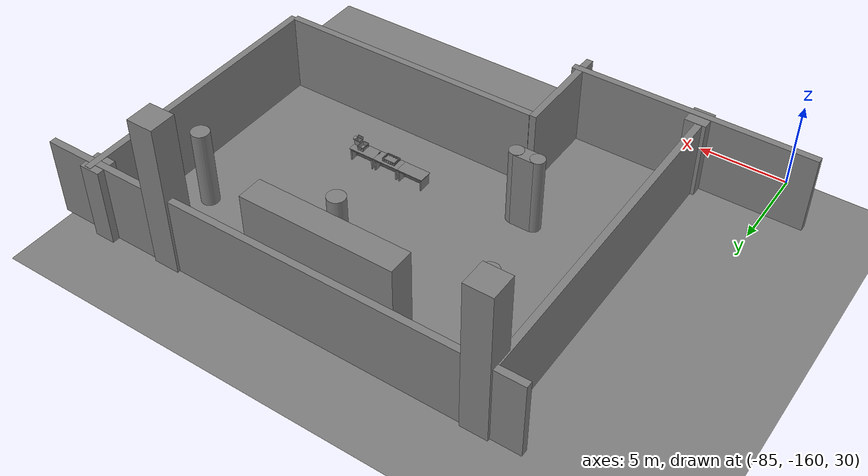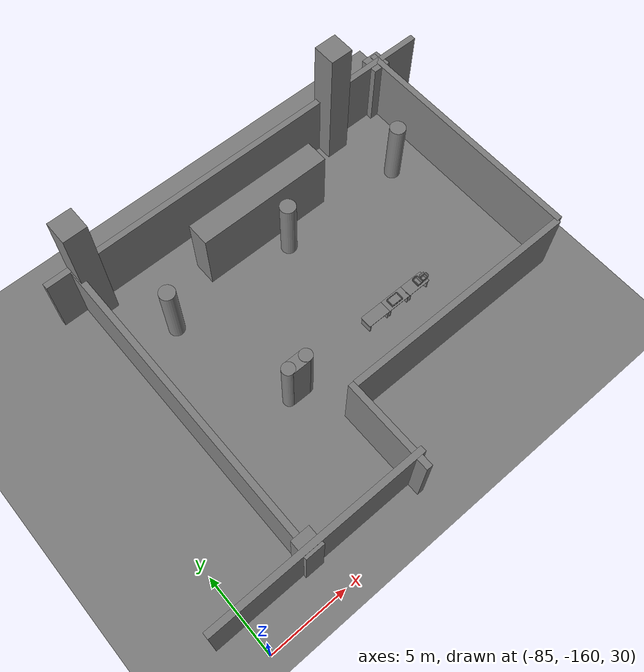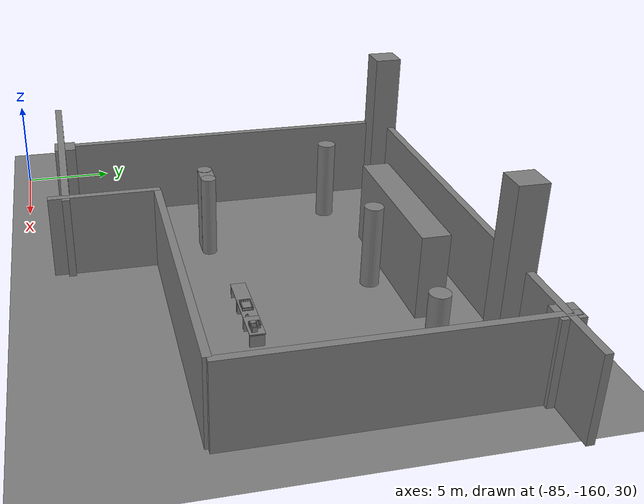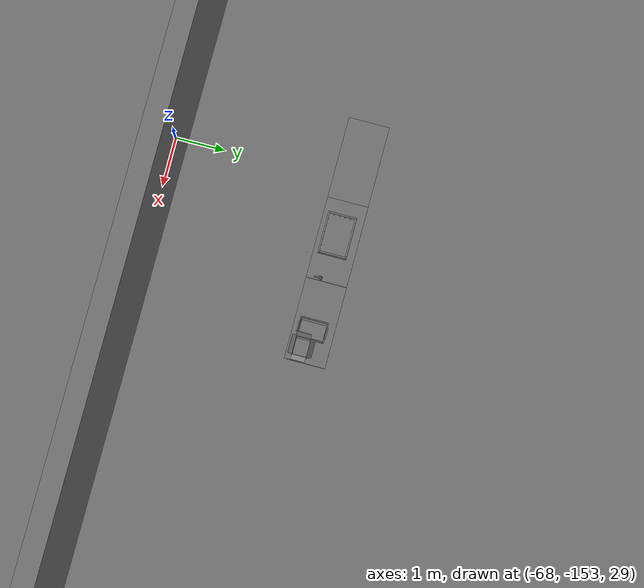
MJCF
<mujoco>
    <option gravity="0.000000000 0.000000000 -9.810000420" timestep="0.0049999999" integrator="implicitfast" density="1.225" viscosity="1.8000001e-05" noslip_iterations="10" iterations="100" sdf_iterations="50">
        <flag multiccd="disable"/>
    </option>
    <size memory="1000M"/>
    <compiler coordinate="local"/>
    <worldbody>
        <light cutoff="30" pos="0 1 1" dir="0 -1 -2"/>
        <light cutoff="30" pos="0 -1 1" dir="0 1 -2"/>
        <body pos="-64.866622925 -149.383972168 30.183746338" euler="89.999992371 89.999946594 0.000000000" name="openloong_gripper_2f85_fix_base_usda_bluebox_01">
            <geom contype="1" conaffinity="1" density="1000" type="box" material="" rgba="0.500000000 0.500000000 0.500000000 1.000000000" solimp="0.899999976 0.949999988 0.001000000" friction="1.000000000 0.005000000 0.000100000" solref="0.020000000 1.000000000" margin="0" condim="3" group="0" pos="0.276596069 0.187225342 0.000061035" quat="0.707107008 0.000077501 0.707106471 0.000077456" size="0.100000001 0.057999998 0.010000000" name="openloong_gripper_2f85_fix_base_usda_geom_2CBBF048_EE8E_4472_8954_A4CB9CC7A424"/>
            <geom contype="1" conaffinity="1" density="1000" type="box" material="" rgba="0.500000000 0.500000000 0.500000000 1.000000000" solimp="0.899999976 0.949999988 0.001000000" friction="1.000000000 0.005000000 0.000100000" solref="0.020000000 1.000000000" margin="0" condim="3" group="0" pos="0.000000000 0.002883911 0.000000000" quat="1.000000000 0.000000000 0.000000000 0.000000000" size="0.254000008 0.003000000 0.172000006" name="openloong_gripper_2f85_fix_base_usda_geom_2C674300_77A2_42EF_A48D_D7DFC01E2ED0"/>
            <geom contype="1" conaffinity="1" density="1000" type="box" material="" rgba="0.500000000 0.500000000 0.500000000 1.000000000" solimp="0.899999976 0.949999988 0.001000000" friction="1.000000000 0.005000000 0.000100000" solref="0.020000000 1.000000000" margin="0" condim="3" group="0" pos="0.000015259 0.124874115 0.173477173" quat="0.999796450 0.020176515 -0.000000015 0.000000030" size="0.259999990 0.119999997 0.007000000" name="openloong_gripper_2f85_fix_base_usda_geom_AABC6BD4_0230_45E1_A82C_B915972E743B"/>
            <geom contype="1" conaffinity="1" density="1000" type="box" material="" rgba="0.500000000 0.500000000 0.500000000 1.000000000" solimp="0.899999976 0.949999988 0.001000000" friction="1.000000000 0.005000000 0.000100000" solref="0.020000000 1.000000000" margin="0" condim="3" group="0" pos="0.000015259 0.124874115 -0.173477173" quat="0.999796450 -0.020176545 -0.000000015 0.000000000" size="0.259999990 0.119999997 0.007000000" name="openloong_gripper_2f85_fix_base_usda_geom_B02E743C_219E_4333_8D03_5DE305DAAB69"/>
            <geom contype="1" conaffinity="1" density="1000" type="box" material="" rgba="0.500000000 0.500000000 0.500000000 1.000000000" solimp="0.899999976 0.949999988 0.001000000" friction="1.000000000 0.005000000 0.000100000" solref="0.020000000 1.000000000" margin="0" condim="3" group="0" pos="0.000015259 0.214012146 0.188980103" quat="0.999913096 0.013176724 0.000000015 0.000000000" size="0.259999990 0.029999999 0.012500000" name="openloong_gripper_2f85_fix_base_usda_geom_78B51291_AE2D_4842_9EBE_DA7E4474EF14"/>
            <geom contype="1" conaffinity="1" density="1000" type="box" material="" rgba="0.500000000 0.500000000 0.500000000 1.000000000" solimp="0.899999976 0.949999988 0.001000000" friction="1.000000000 0.005000000 0.000100000" solref="0.020000000 1.000000000" margin="0" condim="3" group="0" pos="-0.258346558 0.125289917 0.001876831" quat="0.702796996 -0.020792052 0.710783184 0.020769238" size="0.189999998 0.119999997 0.009000000" name="openloong_gripper_2f85_fix_base_usda_geom_698FE9B9_76FC_42C5_839D_A1FA79B5EE17"/>
            <geom contype="1" conaffinity="1" density="1000" type="box" material="" rgba="0.500000000 0.500000000 0.500000000 1.000000000" solimp="0.899999976 0.949999988 0.001000000" friction="1.000000000 0.005000000 0.000100000" solref="0.020000000 1.000000000" margin="0" condim="3" group="0" pos="0.000015259 0.214012146 -0.188980103" quat="0.999913096 -0.013176769 0.000000030 0.000000015" size="0.259999990 0.029999999 0.012500000" name="openloong_gripper_2f85_fix_base_usda_geom_E4E4472A_07E2_4A17_87E9_A61E211B543F"/>
            <geom contype="1" conaffinity="1" density="1000" type="box" material="" rgba="0.500000000 0.500000000 0.500000000 1.000000000" solimp="0.899999976 0.949999988 0.001000000" friction="1.000000000 0.005000000 0.000100000" solref="0.020000000 1.000000000" margin="0" condim="3" group="0" pos="-0.276596069 0.187225342 0.000061035" quat="0.707106650 0.000077441 0.707106709 0.000077456" size="0.100000001 0.057999998 0.010000000" name="openloong_gripper_2f85_fix_base_usda_geom_B80ACC3D_BF5E_4D79_A4BE_6E2964D01F78"/>
            <geom contype="1" conaffinity="1" density="1000" type="box" material="" rgba="0.500000000 0.500000000 0.500000000 1.000000000" solimp="0.899999976 0.949999988 0.001000000" friction="1.000000000 0.005000000 0.000100000" solref="0.020000000 1.000000000" margin="0" condim="3" group="0" pos="0.258346558 0.125289917 0.001876831" quat="0.702851534 0.018856451 0.710823834 -0.019329429" size="0.189999998 0.119999997 0.009000000" name="openloong_gripper_2f85_fix_base_usda_geom_E11D243D_1D9C_4544_AF77_F5A6A40B2F3A"/>
            <freejoint name="openloong_gripper_2f85_fix_base_usda_bluebox_01_joint"/>
            <site size="0.005000000 0.005000000 0.005000000" rgba="0.500000000 0.500000000 0.500000000 1.000000000" pos="0.000000000 0.000000000 0.000000000" quat="0.999961913 0.008726534 0.000000000 0.000000000" group="0" type="sphere" name="openloong_gripper_2f85_fix_base_usda_bluebox_01site"/>
        </body>
        <body pos="-64.496299744 -149.491867065 30.235729218" euler="0.000000000 0.000000000 89.999946594" name="openloong_gripper_2f85_fix_base_usda_cardboardbox_01">
            <geom contype="1" conaffinity="1" density="1000" type="box" material="" rgba="0.500000000 0.500000000 0.500000000 1.000000000" solimp="0.899999976 0.949999988 0.001000000" friction="1.000000000 0.005000000 0.000100000" solref="0.020000000 1.000000000" margin="0" condim="3" group="0" pos="-0.003166199 -0.004086494 0.005052090" quat="1.000000000 0.000000000 0.000000000 0.000000000" size="0.142499998 0.177500010 0.005000000" name="openloong_gripper_2f85_fix_base_usda_geom_E4D85400_60F6_4704_BFBA_3A1FFFDCE1C6"/>
            <geom contype="1" conaffinity="1" density="1000" type="box" material="" rgba="0.500000000 0.500000000 0.500000000 1.000000000" solimp="0.899999976 0.949999988 0.001000000" friction="1.000000000 0.005000000 0.000100000" solref="0.020000000 1.000000000" margin="0" condim="3" group="0" pos="-0.003166199 0.170316696 0.150570869" quat="1.000000000 0.000000000 0.000000000 0.000000000" size="0.142499998 0.005000000 0.149999991" name="openloong_gripper_2f85_fix_base_usda_geom_5536E4E7_739F_4AD0_BD25_C39A011B54C4"/>
            <geom contype="1" conaffinity="1" density="1000" type="box" material="" rgba="0.500000000 0.500000000 0.500000000 1.000000000" solimp="0.899999976 0.949999988 0.001000000" friction="1.000000000 0.005000000 0.000100000" solref="0.020000000 1.000000000" margin="0" condim="3" group="0" pos="-0.147399902 -0.005307198 0.150570869" quat="1.000000000 0.000000000 0.000000000 0.000000000" size="0.005000000 0.177500010 0.149999991" name="openloong_gripper_2f85_fix_base_usda_geom_3E1CA0DC_40F3_4680_96B5_816650942F4A"/>
            <geom contype="1" conaffinity="1" density="1000" type="box" material="" rgba="0.500000000 0.500000000 0.500000000 1.000000000" solimp="0.899999976 0.949999988 0.001000000" friction="1.000000000 0.005000000 0.000100000" solref="0.020000000 1.000000000" margin="0" condim="3" group="0" pos="0.140275955 -0.005307198 0.150570869" quat="1.000000000 0.000000000 0.000000000 0.000000000" size="0.005000000 0.177500010 0.149999991" name="openloong_gripper_2f85_fix_base_usda_geom_94FB893C_9D69_4522_A3CF_7B89519FF4E3"/>
            <geom contype="1" conaffinity="1" density="1000" type="box" material="" rgba="0.500000000 0.500000000 0.500000000 1.000000000" solimp="0.899999976 0.949999988 0.001000000" friction="1.000000000 0.005000000 0.000100000" solref="0.020000000 1.000000000" margin="0" condim="3" group="0" pos="-0.003166199 -0.181550980 0.150570869" quat="1.000000000 0.000000000 0.000000000 0.000000000" size="0.142499998 0.005000000 0.149999991" name="openloong_gripper_2f85_fix_base_usda_geom_67CBEB7A_3081_4932_A143_C0B48A98B145"/>
            <freejoint name="openloong_gripper_2f85_fix_base_usda_cardboardbox_01_joint"/>
            <site size="0.005000000 0.005000000 0.005000000" rgba="0.500000000 0.500000000 0.500000000 1.000000000" pos="0.000000000 0.000000000 0.000000000" quat="0.999961913 0.008726535 0.000000000 0.000000000" group="0" type="sphere" name="openloong_gripper_2f85_fix_base_usda_site_8EA92FAD_30E9_4126_A996_2FC42556A0F8"/>
            <body pos="0.139160156 -0.004048347 0.301930904" euler="-179.999954224 49.383502960 179.999954224" name="openloong_gripper_2f85_fix_base_usda_A1_006">
                <geom contype="1" conaffinity="1" density="1000" type="box" material="" rgba="0.500000000 0.500000000 0.500000000 1.000000000" solimp="0.899999976 0.949999988 0.001000000" friction="1.000000000 0.005000000 0.000100000" solref="0.020000000 1.000000000" margin="0" condim="3" group="0" pos="-0.071587563 0.000009537 0.001745224" quat="0.999999881 0.000000000 0.000000000 0.000000000" size="0.071249999 0.179999992 0.002500000" name="openloong_gripper_2f85_fix_base_usda_geom_19F4DC05_1C7E_4EC0_8028_D201522A6F51"/>
                <joint armature="0" stiffness="0.07" damping="0.0099999998" axis="0.000000 1.000000 0.000000" type="hinge" name="openloong_gripper_2f85_fix_base_usda_A1_006"/>
            </body>
            <body pos="-0.145902634 -0.004086494 0.301938057" euler="-180.000000000 -60.000011444 -180.000000000" name="openloong_gripper_2f85_fix_base_usda_A2_006">
                <geom contype="1" conaffinity="1" density="1000" type="box" material="" rgba="0.500000000 0.500000000 0.500000000 1.000000000" solimp="0.899999976 0.949999988 0.001000000" friction="1.000000000 0.005000000 0.000100000" solref="0.020000000 1.000000000" margin="0" condim="3" group="0" pos="0.071268082 0.000009537 0.002717972" quat="0.000002921 0.000000000 -0.000000030 0.999999881" size="0.071249999 0.179999992 0.002500000" name="openloong_gripper_2f85_fix_base_usda_geom_2DAEF162_C0C3_4BE8_8E3D_324AC49A507C"/>
                <joint armature="0" stiffness="0.07" damping="0.0099999998" axis="0.000000 1.000000 0.000000" type="hinge" name="openloong_gripper_2f85_fix_base_usda_A2_006"/>
            </body>
            <body pos="-0.003385544 0.175991058 0.301930904" euler="-125.858116150 -0.000004561 0.000002331" name="openloong_gripper_2f85_fix_base_usda_B2_006">
                <geom contype="1" conaffinity="1" density="1000" type="box" material="" rgba="0.500000000 0.500000000 0.500000000 1.000000000" solimp="0.899999976 0.949999988 0.001000000" friction="1.000000000 0.005000000 0.000100000" solref="0.020000000 1.000000000" margin="0" condim="3" group="0" pos="0.000009537 -0.070939064 -0.002470016" quat="0.999614120 0.027776197 -0.000000015 0.000000030" size="0.137500003 0.064999998 0.005000000" name="openloong_gripper_2f85_fix_base_usda_geom_535B064F_59F5_4CE7_AAD0_5265ABD51A6B"/>
                <joint armature="0" stiffness="0.07" damping="0.0099999998" axis="1.000000 0.000000 0.000000" type="hinge" name="openloong_gripper_2f85_fix_base_usda_B2_006"/>
            </body>
            <body pos="-0.003385544 -0.184140205 0.301938057" euler="147.805557251 0.000000000 0.000000000" name="openloong_gripper_2f85_fix_base_usda_B1_006">
                <geom contype="1" conaffinity="1" density="1000" type="box" material="" rgba="0.500000000 0.500000000 0.500000000 1.000000000" solimp="0.899999976 0.949999988 0.001000000" friction="1.000000000 0.005000000 0.000100000" solref="0.020000000 1.000000000" margin="0" condim="3" group="0" pos="-0.000028610 0.070202351 -0.002703667" quat="0.999614179 -0.027776167 0.000000000 0.000000000" size="0.137500003 0.064999998 0.005000000" name="openloong_gripper_2f85_fix_base_usda_geom_9FC2F0AA_FD08_41C5_AE5A_DA7510628B5C"/>
                <joint armature="0" stiffness="0.07" damping="0.0099999998" axis="1.000000 0.000000 0.000000" type="hinge" name="openloong_gripper_2f85_fix_base_usda_B1_006"/>
            </body>
        </body>
        <body pos="-65.882858276 -149.481979370 30.229999542" euler="-64.487716675 0.000000000 0.000000000" name="openloong_gripper_2f85_fix_base_usda_Barcode">
            <geom contype="1" conaffinity="1" density="1000" type="box" material="" rgba="0.500000000 0.500000000 0.500000000 1.000000000" solimp="0.899999976 0.949999988 0.001000000" friction="1.000000000 0.005000000 0.000100000" solref="0.020000000 1.000000000" margin="0" condim="3" group="0" pos="0.000000000 0.013038635 0.001419067" quat="0.000000000 0.000000000 0.000000000 1.000000119" size="0.034000002 0.010000000 0.017999999" name="openloong_gripper_2f85_fix_base_usda_geom_5809C4B0_1D47_4B66_BEEA_E35792F10F7A"/>
            <geom contype="1" conaffinity="1" density="1000" type="box" material="" rgba="0.500000000 0.500000000 0.500000000 1.000000000" solimp="0.899999976 0.949999988 0.001000000" friction="1.000000000 0.005000000 0.000100000" solref="0.020000000 1.000000000" margin="0" condim="3" group="0" pos="0.000000000 -0.035301208 -0.007095337" quat="0.000000000 0.000000000 -0.043619365 0.999048233" size="0.028999999 0.010000000 0.020000000" name="openloong_gripper_2f85_fix_base_usda_geom_7B4A814B_9C7A_457D_A0A3_B3633B0DB8DC"/>
            <geom contype="1" conaffinity="1" density="1000" type="box" material="" rgba="0.500000000 0.500000000 0.500000000 1.000000000" solimp="0.899999976 0.949999988 0.001000000" friction="1.000000000 0.005000000 0.000100000" solref="0.020000000 1.000000000" margin="0" condim="3" group="0" pos="0.000000000 -0.043411255 -0.011749268" quat="0.922262907 0.386563420 0.000000000 0.000000000" size="0.026000001 0.010000000 0.020000000" name="openloong_gripper_2f85_fix_base_usda_geom_9B7C547E_64D8_4466_9E34_1254C3E51AC6"/>
            <geom contype="1" conaffinity="1" density="1000" type="box" material="" rgba="0.500000000 0.500000000 0.500000000 1.000000000" solimp="0.899999976 0.949999988 0.001000000" friction="1.000000000 0.005000000 0.000100000" solref="0.020000000 1.000000000" margin="0" condim="3" group="0" pos="0.000000000 -0.016967773 -0.031860352" quat="0.000000000 0.000000000 0.000000000 1.000000119" size="0.008000000 0.010000000 0.013000000" name="openloong_gripper_2f85_fix_base_usda_geom_107600A1_2381_4576_9EEF_8B64C7C557E9"/>
            <geom contype="1" conaffinity="1" density="1000" type="box" material="" rgba="0.500000000 0.500000000 0.500000000 1.000000000" solimp="0.899999976 0.949999988 0.001000000" friction="1.000000000 0.005000000 0.000100000" solref="0.020000000 1.000000000" margin="0" condim="3" group="0" pos="0.000000000 -0.001869202 0.000312805" quat="0.953716993 0.300705761 0.000000000 0.000000000" size="0.032000002 0.010000000 0.018999999" name="openloong_gripper_2f85_fix_base_usda_geom_C9F318A5_0BC6_45CD_B8FA_31D1EDD2725F"/>
            <geom contype="1" conaffinity="1" density="1000" type="box" material="" rgba="0.500000000 0.500000000 0.500000000 1.000000000" solimp="0.899999976 0.949999988 0.001000000" friction="1.000000000 0.005000000 0.000100000" solref="0.020000000 1.000000000" margin="0" condim="3" group="0" pos="0.000000000 -0.019531250 -0.003173828" quat="0.953716993 0.300705761 0.000000000 0.000000000" size="0.030999999 0.010000000 0.020000000" name="openloong_gripper_2f85_fix_base_usda_geom_279F6772_DECF_430E_9908_F3E2E4B249D0"/>
            <geom contype="1" conaffinity="1" density="1000" type="box" material="" rgba="0.500000000 0.500000000 0.500000000 1.000000000" solimp="0.899999976 0.949999988 0.001000000" friction="1.000000000 0.005000000 0.000100000" solref="0.020000000 1.000000000" margin="0" condim="3" group="0" pos="0.000000000 -0.035301208 -0.007095337" quat="0.953716993 0.300705761 0.000000000 0.000000000" size="0.028999999 0.010000000 0.020000000" name="openloong_gripper_2f85_fix_base_usda_geom_9A9F4B6B_B78E_4994_B4F3_AE3960C1619B"/>
            <geom contype="1" conaffinity="1" density="1000" type="box" material="" rgba="0.500000000 0.500000000 0.500000000 1.000000000" solimp="0.899999976 0.949999988 0.001000000" friction="1.000000000 0.005000000 0.000100000" solref="0.020000000 1.000000000" margin="0" condim="3" group="0" pos="0.000000000 -0.042617798 -0.071121216" quat="0.000000000 0.000000000 0.000000000 1.000000119" size="0.013000000 0.021000000 0.059999999" name="openloong_gripper_2f85_fix_base_usda_geom_2FF05035_E4AF_40CD_9395_F1BD5583EBE1"/>
            <freejoint name="openloong_gripper_2f85_fix_base_usda_Barcode_joint"/>
            <site size="0.005000000 0.005000000 0.005000000" rgba="0.500000000 0.500000000 0.500000000 1.000000000" pos="0.000000000 0.000000000 0.000000000" quat="1.000000000 0.000000000 0.000000000 0.000000000" group="0" type="sphere" name="openloong_gripper_2f85_fix_base_usda_Barcode_site"/>
        </body>
        <body pos="-66.745018005 -149.392349243 30.184000015" euler="0.000000000 0.000000000 89.999946594" name="[22331731856570]_Basket_01">
            <geom contype="1" conaffinity="1" density="1000" type="box" material="" rgba="0.500000000 0.500000000 0.500000000 1.000000000" solimp="0.899999976 0.949999988 0.001000000" friction="1.000000000 0.005000000 0.000100000" solref="0.020000000 1.000000000" margin="0" condim="3" group="0" pos="-0.052425385 0.389207840 0.089787483" quat="0.707107008 0.000000000 0.000000000 0.707106411" size="0.014249999 0.014249999 0.059999999" name="[22331731856570]_geom_0042E534_C032_410F_82A9_B9E2CF5E65F2"/>
            <geom contype="1" conaffinity="1" density="1000" type="box" material="" rgba="0.500000000 0.500000000 0.500000000 1.000000000" solimp="0.899999976 0.949999988 0.001000000" friction="1.000000000 0.005000000 0.000100000" solref="0.020000000 1.000000000" margin="0" condim="3" group="0" pos="0.264015198 -0.133043289 0.089787483" quat="0.707107008 0.000000000 0.000000000 0.707106411" size="0.014249999 0.014249999 0.059999999" name="[22331731856570]_geom_44F0F40D_12D5_4F36_B2C2_10171784E3CB"/>
            <geom contype="1" conaffinity="1" density="1000" type="box" material="" rgba="0.500000000 0.500000000 0.500000000 1.000000000" solimp="0.899999976 0.949999988 0.001000000" friction="1.000000000 0.005000000 0.000100000" solref="0.020000000 1.000000000" margin="0" condim="3" group="0" pos="-0.264015198 -0.265548706 0.089793205" quat="0.707107008 0.000000000 0.000000000 0.707106411" size="0.014249999 0.014249999 0.059999999" name="[22331731856570]_geom_F42FEC4A_2CA7_48A2_97CC_50D048EBE83B"/>
            <geom contype="1" conaffinity="1" density="1000" type="box" material="" rgba="0.500000000 0.500000000 0.500000000 1.000000000" solimp="0.899999976 0.949999988 0.001000000" friction="1.000000000 0.005000000 0.000100000" solref="0.020000000 1.000000000" margin="0" condim="3" group="0" pos="-0.160263062 -0.389322281 0.089793205" quat="0.707107008 0.000000000 0.000000000 0.707106411" size="0.014249999 0.014249999 0.059999999" name="[22331731856570]_geom_53503478_11CC_4371_ABA1_A3AEC39811CE"/>
            <geom contype="1" conaffinity="1" density="1000" type="box" material="" rgba="0.500000000 0.500000000 0.500000000 1.000000000" solimp="0.899999976 0.949999988 0.001000000" friction="1.000000000 0.005000000 0.000100000" solref="0.020000000 1.000000000" margin="0" condim="3" group="0" pos="0.162265778 -0.389322281 0.089787483" quat="0.707107008 0.000000000 0.000000000 0.707106411" size="0.014249999 0.014249999 0.059999999" name="[22331731856570]_geom_A021F3F0_7FC8_4CFF_80AA_C2D8D7E04977"/>
            <geom contype="1" conaffinity="1" density="1000" type="box" material="" rgba="0.500000000 0.500000000 0.500000000 1.000000000" solimp="0.899999976 0.949999988 0.001000000" friction="1.000000000 0.005000000 0.000100000" solref="0.020000000 1.000000000" margin="0" condim="3" group="0" pos="0.264015198 0.389207840 0.089787483" quat="0.707107008 0.000000000 0.000000000 0.707106411" size="0.014249999 0.014249999 0.059999999" name="[22331731856570]_geom_F9E9723C_A652_47C5_9EFE_1ED294D4066F"/>
            <geom contype="1" conaffinity="1" density="1000" type="box" material="" rgba="0.500000000 0.500000000 0.500000000 1.000000000" solimp="0.899999976 0.949999988 0.001000000" friction="1.000000000 0.005000000 0.000100000" solref="0.020000000 1.000000000" margin="0" condim="3" group="0" pos="-0.264015198 -0.133043289 0.089793205" quat="0.707107008 0.000000000 0.000000000 0.707106411" size="0.014249999 0.014249999 0.059999999" name="[22331731856570]_geom_39518342_24E1_478B_98FA_755D3E0CD358"/>
            <geom contype="1" conaffinity="1" density="1000" type="box" material="" rgba="0.500000000 0.500000000 0.500000000 1.000000000" solimp="0.899999976 0.949999988 0.001000000" friction="1.000000000 0.005000000 0.000100000" solref="0.020000000 1.000000000" margin="0" condim="3" group="0" pos="-0.264026642 0.269256592 0.089793205" quat="0.707107008 0.000000000 0.000000000 0.707106411" size="0.014249999 0.014249999 0.059999999" name="[22331731856570]_geom_3D5C162E_139E_4E65_965B_1D10C91C0220"/>
            <geom contype="1" conaffinity="1" density="1000" type="box" material="" rgba="0.500000000 0.500000000 0.500000000 1.000000000" solimp="0.899999976 0.949999988 0.001000000" friction="1.000000000 0.005000000 0.000100000" solref="0.020000000 1.000000000" margin="0" condim="3" group="0" pos="0.054462433 0.389207840 0.089787483" quat="0.707107008 0.000000000 0.000000000 0.707106411" size="0.014249999 0.014249999 0.059999999" name="[22331731856570]_geom_61399C99_3CEF_451C_8534_D859383BC2A2"/>
            <geom contype="1" conaffinity="1" density="1000" type="box" material="" rgba="0.500000000 0.500000000 0.500000000 1.000000000" solimp="0.899999976 0.949999988 0.001000000" friction="1.000000000 0.005000000 0.000100000" solref="0.020000000 1.000000000" margin="0" condim="3" group="0" pos="0.054462433 -0.389322281 0.089787483" quat="0.707107008 0.000000000 0.000000000 0.707106411" size="0.014249999 0.014249999 0.059999999" name="[22331731856570]_geom_E00D1183_4E6F_4FA6_BE0D_2B0466569343"/>
            <geom contype="1" conaffinity="1" density="1000" type="box" material="" rgba="0.500000000 0.500000000 0.500000000 1.000000000" solimp="0.899999976 0.949999988 0.001000000" friction="1.000000000 0.005000000 0.000100000" solref="0.020000000 1.000000000" margin="0" condim="3" group="0" pos="0.264015198 0.269256592 0.089793205" quat="0.707107008 0.000000000 0.000000000 0.707106411" size="0.014249999 0.014249999 0.059999999" name="[22331731856570]_geom_DFD84094_02B9_4641_88B9_D49B7C55FB94"/>
            <geom contype="1" conaffinity="1" density="1000" type="box" material="" rgba="0.500000000 0.500000000 0.500000000 1.000000000" solimp="0.899999976 0.949999988 0.001000000" friction="1.000000000 0.005000000 0.000100000" solref="0.020000000 1.000000000" margin="0" condim="3" group="0" pos="0.264015198 -0.389322281 0.089787483" quat="0.707107008 0.000000000 0.000000000 0.707106411" size="0.014249999 0.014249999 0.059999999" name="[22331731856570]_geom_957A9870_FE03_4F9F_BDAA_BD140C81CF81"/>
            <geom contype="1" conaffinity="1" density="1000" type="box" material="" rgba="0.500000000 0.500000000 0.500000000 1.000000000" solimp="0.899999976 0.949999988 0.001000000" friction="1.000000000 0.005000000 0.000100000" solref="0.020000000 1.000000000" margin="0" condim="3" group="0" pos="0.000000000 0.000000000 0.015998840" quat="0.707107008 0.000000000 0.000000000 0.707106411" size="0.403499991 0.279000014 0.015750000" name="[22331731856570]_geom_66CBD1C5_2390_41DC_962F_12F3F5E4AB4C"/>
            <geom contype="1" conaffinity="1" density="1000" type="box" material="" rgba="0.500000000 0.500000000 0.500000000 1.000000000" solimp="0.899999976 0.949999988 0.001000000" friction="1.000000000 0.005000000 0.000100000" solref="0.020000000 1.000000000" margin="0" condim="3" group="0" pos="0.000000000 -0.389476776 0.163619041" quat="0.707107008 0.000000000 0.000000000 0.707106411" size="0.015000000 0.277500004 0.015750000" name="[22331731856570]_geom_EA9D5B37_7CC9_481A_8D3D_77366E623D20"/>
            <geom contype="1" conaffinity="1" density="1000" type="box" material="" rgba="0.500000000 0.500000000 0.500000000 1.000000000" solimp="0.899999976 0.949999988 0.001000000" friction="1.000000000 0.005000000 0.000100000" solref="0.020000000 1.000000000" margin="0" condim="3" group="0" pos="0.162265778 0.389207840 0.089787483" quat="0.707107008 0.000000000 0.000000000 0.707106411" size="0.014249999 0.014249999 0.059999999" name="[22331731856570]_geom_E6F3EB73_F120_4ED7_ABB1_9E0A908F9001"/>
            <geom contype="1" conaffinity="1" density="1000" type="box" material="" rgba="0.500000000 0.500000000 0.500000000 1.000000000" solimp="0.899999976 0.949999988 0.001000000" friction="1.000000000 0.005000000 0.000100000" solref="0.020000000 1.000000000" margin="0" condim="3" group="0" pos="0.000000000 0.389471054 0.163619041" quat="0.707107008 0.000000000 0.000000000 0.707106411" size="0.015000000 0.277500004 0.015750000" name="[22331731856570]_geom_D3458F5E_8A3E_4DDB_9F81_85F1BFFCEA47"/>
            <geom contype="1" conaffinity="1" density="1000" type="box" material="" rgba="0.500000000 0.500000000 0.500000000 1.000000000" solimp="0.899999976 0.949999988 0.001000000" friction="1.000000000 0.005000000 0.000100000" solref="0.020000000 1.000000000" margin="0" condim="3" group="0" pos="-0.263511658 0.000000000 0.163619041" quat="0.707107008 0.000000000 0.000000000 0.707106411" size="0.403499991 0.015000000 0.015750000" name="[22331731856570]_geom_396A837F_E151_42A5_8F32_4700D6CC4895"/>
            <geom contype="1" conaffinity="1" density="1000" type="box" material="" rgba="0.500000000 0.500000000 0.500000000 1.000000000" solimp="0.899999976 0.949999988 0.001000000" friction="1.000000000 0.005000000 0.000100000" solref="0.020000000 1.000000000" margin="0" condim="3" group="0" pos="-0.264015198 0.141334534 0.089793205" quat="0.707107008 0.000000000 0.000000000 0.707106411" size="0.014249999 0.014249999 0.059999999" name="[22331731856570]_geom_818D0800_9D37_4B8D_8210_9D529D51EA1B"/>
            <geom contype="1" conaffinity="1" density="1000" type="box" material="" rgba="0.500000000 0.500000000 0.500000000 1.000000000" solimp="0.899999976 0.949999988 0.001000000" friction="1.000000000 0.005000000 0.000100000" solref="0.020000000 1.000000000" margin="0" condim="3" group="0" pos="0.264015198 -0.265548706 0.089787483" quat="0.707107008 0.000000000 0.000000000 0.707106411" size="0.014249999 0.014249999 0.059999999" name="[22331731856570]_geom_26084FFD_6DE2_4368_9461_B0437743FAAA"/>
            <geom contype="1" conaffinity="1" density="1000" type="box" material="" rgba="0.500000000 0.500000000 0.500000000 1.000000000" solimp="0.899999976 0.949999988 0.001000000" friction="1.000000000 0.005000000 0.000100000" solref="0.020000000 1.000000000" margin="0" condim="3" group="0" pos="-0.160263062 0.389207840 0.089787483" quat="0.707107008 0.000000000 0.000000000 0.707106411" size="0.014249999 0.014249999 0.059999999" name="[22331731856570]_geom_3D9ADEBC_246F_4D68_B5DD_BA0F173A600F"/>
            <geom contype="1" conaffinity="1" density="1000" type="box" material="" rgba="0.500000000 0.500000000 0.500000000 1.000000000" solimp="0.899999976 0.949999988 0.001000000" friction="1.000000000 0.005000000 0.000100000" solref="0.020000000 1.000000000" margin="0" condim="3" group="0" pos="-0.052425385 -0.389322281 0.089787483" quat="0.707107008 0.000000000 0.000000000 0.707106411" size="0.014249999 0.014249999 0.059999999" name="[22331731856570]_geom_43BF9A9D_82EF_4BF2_B432_05D976845E6C"/>
            <geom contype="1" conaffinity="1" density="1000" type="box" material="" rgba="0.500000000 0.500000000 0.500000000 1.000000000" solimp="0.899999976 0.949999988 0.001000000" friction="1.000000000 0.005000000 0.000100000" solref="0.020000000 1.000000000" margin="0" condim="3" group="0" pos="-0.264026642 -0.389322281 0.089793205" quat="0.707107008 0.000000000 0.000000000 0.707106411" size="0.014249999 0.014249999 0.059999999" name="[22331731856570]_geom_5B97EF11_A8A2_40A4_A41B_20D6476216DD"/>
            <geom contype="1" conaffinity="1" density="1000" type="box" material="" rgba="0.500000000 0.500000000 0.500000000 1.000000000" solimp="0.899999976 0.949999988 0.001000000" friction="1.000000000 0.005000000 0.000100000" solref="0.020000000 1.000000000" margin="0" condim="3" group="0" pos="0.264015198 0.141334534 0.089787483" quat="0.707107008 0.000000000 0.000000000 0.707106411" size="0.014249999 0.014249999 0.059999999" name="[22331731856570]_geom_C47B43AE_35E7_4539_9394_C3A4FFB66E84"/>
            <geom contype="1" conaffinity="1" density="1000" type="box" material="" rgba="0.500000000 0.500000000 0.500000000 1.000000000" solimp="0.899999976 0.949999988 0.001000000" friction="1.000000000 0.005000000 0.000100000" solref="0.020000000 1.000000000" margin="0" condim="3" group="0" pos="-0.264015198 0.389207840 0.089793205" quat="0.707107008 0.000000000 0.000000000 0.707106411" size="0.014249999 0.014249999 0.059999999" name="[22331731856570]_geom_ADD27AD0_FD4A_4BF2_A219_15D1C6BA4761"/>
            <geom contype="1" conaffinity="1" density="1000" type="box" material="" rgba="0.500000000 0.500000000 0.500000000 1.000000000" solimp="0.899999976 0.949999988 0.001000000" friction="1.000000000 0.005000000 0.000100000" solref="0.020000000 1.000000000" margin="0" condim="3" group="0" pos="0.264015198 0.004480362 0.089787483" quat="0.707107008 0.000000000 0.000000000 0.707106411" size="0.014249999 0.014249999 0.059999999" name="[22331731856570]_geom_EEACED25_DB0F_4DA0_8915_19CF6366B1F6"/>
            <geom contype="1" conaffinity="1" density="1000" type="box" material="" rgba="0.500000000 0.500000000 0.500000000 1.000000000" solimp="0.899999976 0.949999988 0.001000000" friction="1.000000000 0.005000000 0.000100000" solref="0.020000000 1.000000000" margin="0" condim="3" group="0" pos="0.263694763 -0.000011444 0.163619041" quat="0.707107008 0.000000000 0.000000000 0.707106411" size="0.403499991 0.015000000 0.015750000" name="[22331731856570]_geom_09137D90_09EE_4827_99D3_9EB9AE00B789"/>
            <geom contype="1" conaffinity="1" density="1000" type="box" material="" rgba="0.500000000 0.500000000 0.500000000 1.000000000" solimp="0.899999976 0.949999988 0.001000000" friction="1.000000000 0.005000000 0.000100000" solref="0.020000000 1.000000000" margin="0" condim="3" group="0" pos="-0.264015198 0.004480362 0.089793205" quat="0.707107008 0.000000000 0.000000000 0.707106411" size="0.014249999 0.014249999 0.059999999" name="[22331731856570]_geom_85D7A1C8_E7D9_4169_850B_E3397B02C12A"/>
            <freejoint name="[22331731856570]_joint_D56A64CA_9E97_4877_B5FC_92FF2526C608"/>
        </body>
        <body pos="0.000000000 0.000000000 0.000000000" euler="0.000000000 0.000000000 0.000000000" name="Static Objects_Static Objects">
            <geom contype="1" conaffinity="1" density="1000" type="box" material="" rgba="0.500000000 0.500000000 0.500000000 1.000000000" solimp="0.899999976 0.949999988 0.001000000" friction="1.000000000 0.005000000 0.000100000" solref="0.020000000 1.000000000" margin="0" condim="3" group="0" pos="-67.544113159 -149.365814209 29.727830887" quat="0.500000417 0.499999970 0.499999553 0.499999970" size="0.381000012 0.319999993 0.041000001" name="Static Objects_geom_833672FE_C811_4555_972D_910CFD637D2D"/>
            <geom contype="1" conaffinity="1" density="1000" type="box" material="" rgba="0.500000000 0.500000000 0.500000000 1.000000000" solimp="0.899999976 0.949999988 0.001000000" friction="1.000000000 0.005000000 0.000100000" solref="0.020000000 1.000000000" margin="0" condim="3" group="0" pos="-68.239501953 -149.365814209 30.086868286" quat="0.500000417 0.499999970 0.499999553 0.499999970" size="0.370999992 0.039500002 0.745000005" name="Static Objects_geom_8F3F8251_F05E_422F_A055_0D215622308B"/>
            <geom contype="1" conaffinity="1" density="1000" type="box" material="" rgba="0.500000000 0.500000000 0.500000000 1.000000000" solimp="0.899999976 0.949999988 0.001000000" friction="1.000000000 0.005000000 0.000100000" solref="0.020000000 1.000000000" margin="0" condim="3" group="0" pos="-68.239501953 -149.365814209 30.147235870" quat="0.500000417 0.499999970 0.499999553 0.499999970" size="0.400000006 0.022000000 0.800000012" name="Static Objects_geom_4544D622_998B_4078_BB59_9990398AAD47"/>
            <geom contype="1" conaffinity="1" density="1000" type="box" material="" rgba="0.500000000 0.500000000 0.500000000 1.000000000" solimp="0.899999976 0.949999988 0.001000000" friction="1.000000000 0.005000000 0.000100000" solref="0.020000000 1.000000000" margin="0" condim="3" group="0" pos="-68.934890747 -149.365814209 29.727830887" quat="0.500000417 0.499999970 0.499999553 0.499999970" size="0.381000012 0.319999993 0.041000001" name="Static Objects_geom_97D34F3B_760C_48E2_8AB5_C22FDBD6E44A"/>
            <geom contype="1" conaffinity="1" density="1000" type="box" material="" rgba="0.500000000 0.500000000 0.500000000 1.000000000" solimp="0.899999976 0.949999988 0.001000000" friction="1.000000000 0.005000000 0.000100000" solref="0.020000000 1.000000000" margin="0" condim="3" group="0" pos="-68.239501953 -149.365814209 29.561563492" quat="0.500000417 0.499999970 0.499999553 0.499999970" size="0.020000000 0.022000000 0.660000026" name="Static Objects_geom_5E329E92_3A04_4453_9385_3B944B1A6233"/>
            <geom contype="1" conaffinity="1" density="1000" type="box" material="" rgba="0.500000000 0.500000000 0.500000000 1.000000000" solimp="0.899999976 0.949999988 0.001000000" friction="1.000000000 0.005000000 0.000100000" solref="0.020000000 1.000000000" margin="0" condim="3" group="0" pos="-65.945671082 -149.365814209 29.727830887" quat="0.500000417 0.499999970 0.499999553 0.499999970" size="0.381000012 0.319999993 0.041000001" name="Static Objects_geom_763C09B4_F054_4F56_B3FC_E586CCFC5C03"/>
            <geom contype="1" conaffinity="1" density="1000" type="box" material="" rgba="0.500000000 0.500000000 0.500000000 1.000000000" solimp="0.899999976 0.949999988 0.001000000" friction="1.000000000 0.005000000 0.000100000" solref="0.020000000 1.000000000" margin="0" condim="3" group="0" pos="-66.641059875 -149.365814209 30.086868286" quat="0.500000417 0.499999970 0.499999553 0.499999970" size="0.370999992 0.039500002 0.745000005" name="Static Objects_geom_CA42AD48_521D_4604_BC3C_637D9E690BCA"/>
            <geom contype="1" conaffinity="1" density="1000" type="box" material="" rgba="0.500000000 0.500000000 0.500000000 1.000000000" solimp="0.899999976 0.949999988 0.001000000" friction="1.000000000 0.005000000 0.000100000" solref="0.020000000 1.000000000" margin="0" condim="3" group="0" pos="-66.641059875 -149.365814209 30.147235870" quat="0.500000417 0.499999970 0.499999553 0.499999970" size="0.400000006 0.022000000 0.800000012" name="Static Objects_geom_A4633783_AAC5_479E_BB6F_1B46D5F2E1DB"/>
            <geom contype="1" conaffinity="1" density="1000" type="box" material="" rgba="0.500000000 0.500000000 0.500000000 1.000000000" solimp="0.899999976 0.949999988 0.001000000" friction="1.000000000 0.005000000 0.000100000" solref="0.020000000 1.000000000" margin="0" condim="3" group="0" pos="-67.336448669 -149.365814209 29.727830887" quat="0.500000417 0.499999970 0.499999553 0.499999970" size="0.381000012 0.319999993 0.041000001" name="Static Objects_geom_12A890E8_D476_4AAB_8CC1_FEFC05F92148"/>
            <geom contype="1" conaffinity="1" density="1000" type="box" material="" rgba="0.500000000 0.500000000 0.500000000 1.000000000" solimp="0.899999976 0.949999988 0.001000000" friction="1.000000000 0.005000000 0.000100000" solref="0.020000000 1.000000000" margin="0" condim="3" group="0" pos="-66.641059875 -149.365814209 29.561563492" quat="0.500000417 0.499999970 0.499999553 0.499999970" size="0.020000000 0.022000000 0.660000026" name="Static Objects_geom_4CD10C1C_B542_4F29_8F16_1806D753C166"/>
            <geom contype="1" conaffinity="1" density="1000" type="box" material="" rgba="0.500000000 0.500000000 0.500000000 1.000000000" solimp="0.899999976 0.949999988 0.001000000" friction="1.000000000 0.005000000 0.000100000" solref="0.020000000 1.000000000" margin="0" condim="3" group="0" pos="-64.338577271 -149.365814209 29.727830887" quat="0.500000417 0.499999970 0.499999553 0.499999970" size="0.381000012 0.319999993 0.041000001" name="Static Objects_geom_F0BD8F33_F6C2_4244_A116_6626E19D094C"/>
            <geom contype="1" conaffinity="1" density="1000" type="box" material="" rgba="0.500000000 0.500000000 0.500000000 1.000000000" solimp="0.899999976 0.949999988 0.001000000" friction="1.000000000 0.005000000 0.000100000" solref="0.020000000 1.000000000" margin="0" condim="3" group="0" pos="-65.033966064 -149.365814209 30.086868286" quat="0.500000417 0.499999970 0.499999553 0.499999970" size="0.370999992 0.039500002 0.745000005" name="Static Objects_geom_50FA92AA_B9D2_4120_8B81_F41015EF1229"/>
            <geom contype="1" conaffinity="1" density="1000" type="box" material="" rgba="0.500000000 0.500000000 0.500000000 1.000000000" solimp="0.899999976 0.949999988 0.001000000" friction="1.000000000 0.005000000 0.000100000" solref="0.020000000 1.000000000" margin="0" condim="3" group="0" pos="-65.033966064 -149.365814209 30.147235870" quat="0.500000417 0.499999970 0.499999553 0.499999970" size="0.400000006 0.022000000 0.800000012" name="Static Objects_geom_40376671_A16F_46F6_AF90_63A8A69C4740"/>
            <geom contype="1" conaffinity="1" density="1000" type="box" material="" rgba="0.500000000 0.500000000 0.500000000 1.000000000" solimp="0.899999976 0.949999988 0.001000000" friction="1.000000000 0.005000000 0.000100000" solref="0.020000000 1.000000000" margin="0" condim="3" group="0" pos="-65.729354858 -149.365814209 29.727830887" quat="0.500000417 0.499999970 0.499999553 0.499999970" size="0.381000012 0.319999993 0.041000001" name="Static Objects_geom_E70F4CD5_1AA3_456C_A232_C257D3BC70F2"/>
            <geom contype="1" conaffinity="1" density="1000" type="box" material="" rgba="0.500000000 0.500000000 0.500000000 1.000000000" solimp="0.899999976 0.949999988 0.001000000" friction="1.000000000 0.005000000 0.000100000" solref="0.020000000 1.000000000" margin="0" condim="3" group="0" pos="-65.033966064 -149.365814209 29.561563492" quat="0.500000417 0.499999970 0.499999553 0.499999970" size="0.020000000 0.022000000 0.660000026" name="Static Objects_geom_7DB34681_75B5_45A6_B9F6_276840DA70D4"/>
            <geom contype="1" conaffinity="1" density="1000" type="box" material="" rgba="0.500000000 0.500000000 0.500000000 1.000000000" solimp="0.899999976 0.949999988 0.001000000" friction="1.000000000 0.005000000 0.000100000" solref="0.020000000 1.000000000" margin="0" condim="3" group="0" pos="-61.754566193 -137.853729248 33.906845093" quat="0.707107067 0.000000000 0.000000000 0.707106471" size="0.759999990 0.759999990 4.500000000" name="Static Objects_geom_670D3DFD_A8F8_4C4C_9F8C_63739BE49CB1"/>
            <geom contype="1" conaffinity="1" density="1000" type="box" material="" rgba="0.500000000 0.500000000 0.500000000 1.000000000" solimp="0.899999976 0.949999988 0.001000000" friction="1.000000000 0.005000000 0.000100000" solref="0.020000000 1.000000000" margin="0" condim="3" group="0" pos="-57.511135101 -144.927108765 31.707921982" quat="1.000000000 0.000000000 0.000000000 0.000000000" size="0.200000003 8.000000000 2.299999952" name="Static Objects_geom_5903D21E_7133_4FE3_ABFD_873FCC271BD8"/>
            <geom contype="1" conaffinity="1" density="1000" type="box" material="" rgba="0.500000000 0.500000000 0.500000000 1.000000000" solimp="0.899999976 0.949999988 0.001000000" friction="1.000000000 0.005000000 0.000100000" solref="0.020000000 1.000000000" margin="0" condim="3" group="0" pos="-80.517646790 -157.574050903 31.688196182" quat="0.707107067 0.000000000 0.000000000 0.707106471" size="0.600000024 0.600000024 2.299999952" name="Static Objects_geom_8BB58ED5_05DB_4642_8276_E8BAD2E40C5A"/>
            <geom contype="1" conaffinity="1" density="1000" type="box" material="" rgba="0.500000000 0.500000000 0.500000000 1.000000000" solimp="0.899999976 0.949999988 0.001000000" friction="1.000000000 0.005000000 0.000100000" solref="0.020000000 1.000000000" margin="0" condim="3" group="0" pos="-80.711044312 -147.414932251 31.666158676" quat="1.000000000 0.000000000 0.000000000 0.000000000" size="0.200000003 10.000000000 2.299999952" name="Static Objects_geom_57992ED2_4E39_406A_82F7_98AD7B62A80F"/>
            <geom contype="1" conaffinity="1" density="1000" type="box" material="" rgba="0.500000000 0.500000000 0.500000000 1.000000000" solimp="0.899999976 0.949999988 0.001000000" friction="1.000000000 0.005000000 0.000100000" solref="0.020000000 1.000000000" margin="0" condim="3" group="0" pos="-57.687217712 -137.434692383 31.688196182" quat="0.707107067 0.000000000 0.000000000 0.707106471" size="0.600000024 0.600000024 2.299999952" name="Static Objects_geom_DEEE1DEC_8616_4075_B824_156C93A44E9E"/>
            <geom contype="1" conaffinity="1" density="1000" type="box" material="" rgba="0.500000000 0.500000000 0.500000000 1.000000000" solimp="0.899999976 0.949999988 0.001000000" friction="1.000000000 0.005000000 0.000100000" solref="0.020000000 1.000000000" margin="0" condim="3" group="0" pos="-69.537033081 -140.263229370 31.714921951" quat="0.707107067 0.000000000 0.000000000 0.707106471" size="0.759999990 4.500000000 2.299999952" name="Static Objects_geom_E9E81789_059B_46A3_B8DB_25090F4187A1"/>
            <geom contype="1" conaffinity="1" density="1000" type="box" material="" rgba="0.500000000 0.500000000 0.500000000 1.000000000" solimp="0.899999976 0.949999988 0.001000000" friction="1.000000000 0.005000000 0.000100000" solref="0.020000000 1.000000000" margin="0" condim="3" group="0" pos="-80.073638916 -137.853713989 33.906845093" quat="0.707107067 0.000000000 0.000000000 0.707106471" size="0.759999990 0.759999990 4.500000000" name="Static Objects_geom_A13A8C2C_1902_4E71_8716_3BBD70818BB1"/>
            <geom contype="1" conaffinity="1" density="1000" type="box" material="" rgba="0.500000000 0.500000000 0.500000000 1.000000000" solimp="0.899999976 0.949999988 0.001000000" friction="1.000000000 0.005000000 0.000100000" solref="0.020000000 1.000000000" margin="0" condim="3" group="0" pos="-73.406707764 -155.734664917 31.707921982" quat="1.000000000 0.000000000 0.000000000 0.000000000" size="0.200000003 3.000000000 2.299999952" name="Static Objects_geom_B5F6C13B_7FD9_4AD9_97C4_96C71951FCFA"/>
            <geom contype="1" conaffinity="1" density="1000" type="box" material="" rgba="0.500000000 0.500000000 0.500000000 1.000000000" solimp="0.899999976 0.949999988 0.001000000" friction="1.000000000 0.005000000 0.000100000" solref="0.020000000 1.000000000" margin="0" condim="3" group="0" pos="-68.497543335 -137.448257446 31.707921982" quat="0.707107067 0.000000000 0.000000000 0.707106471" size="0.200000003 14.000000000 2.299999952" name="Static Objects_geom_967E58B3_8B28_4436_A363_36375199DBEE"/>
            <geom contype="1" conaffinity="1" density="1000" type="cylinder" material="" rgba="0.500000000 0.500000000 0.500000000 1.000000000" solimp="0.899999976 0.949999988 0.001000000" friction="1.000000000 0.005000000 0.000100000" solref="0.020000000 1.000000000" margin="0" condim="3" group="0" pos="-68.868522644 -142.134506226 31.711090088" quat="0.707107067 0.000000000 0.000000000 0.707106471" size="0.509999990 2.299999952 1.000000000" name="Static Objects_geom_16B792D8_61D6_4CFB_87CF_9564D0AE0491"/>
            <geom contype="1" conaffinity="1" density="1000" type="plane" material="" rgba="0.500000000 0.500000000 0.500000000 1.000000000" solimp="0.899999976 0.949999988 0.001000000" friction="1.000000000 0.005000000 0.000100000" solref="0.020000000 1.000000000" margin="0" condim="3" group="0" pos="-72.873703003 -147.131927490 29.409669876" quat="1.000000000 0.000000000 0.000000000 0.000000000" size="18.000000000 14.000000000 1.000000000" name="Static Objects_geom_5C2E5A54_37C9_4B4A_8437_32D1E0298EEC"/>
            <geom contype="1" conaffinity="1" density="1000" type="box" material="" rgba="0.500000000 0.500000000 0.500000000 1.000000000" solimp="0.899999976 0.949999988 0.001000000" friction="1.000000000 0.005000000 0.000100000" solref="0.020000000 1.000000000" margin="0" condim="3" group="0" pos="-79.943580627 -157.782272339 31.707921982" quat="0.707107067 0.000000000 0.000000000 0.707106471" size="0.200000003 7.000000000 2.299999952" name="Static Objects_geom_989ABDE4_185F_4EC2_A5CD_92FCC60FC0F5"/>
            <geom contype="1" conaffinity="1" density="1000" type="box" material="" rgba="0.500000000 0.500000000 0.500000000 1.000000000" solimp="0.899999976 0.949999988 0.001000000" friction="1.000000000 0.005000000 0.000100000" solref="0.020000000 1.000000000" margin="0" condim="3" group="0" pos="-65.421028137 -152.903442383 31.707921982" quat="0.707107067 0.000000000 0.000000000 0.707106471" size="0.200000003 7.800000191 2.299999952" name="Static Objects_geom_2D9E9641_AF4A_407E_A157_687C711C2401"/>
            <geom contype="1" conaffinity="1" density="1000" type="box" material="" rgba="0.500000000 0.500000000 0.500000000 1.000000000" solimp="0.899999976 0.949999988 0.001000000" friction="1.000000000 0.005000000 0.000100000" solref="0.020000000 1.000000000" margin="0" condim="3" group="0" pos="-74.776908875 -149.964416504 31.688196182" quat="1.000000000 0.000000000 0.000000000 0.000000000" size="0.600000024 0.409999996 2.299999952" name="Static Objects_geom_D83D1DEA_E258_4404_9F86_95A744BB055C"/>
            <geom contype="1" conaffinity="1" density="1000" type="cylinder" material="" rgba="0.500000000 0.500000000 0.500000000 1.000000000" solimp="0.899999976 0.949999988 0.001000000" friction="1.000000000 0.005000000 0.000100000" solref="0.020000000 1.000000000" margin="0" condim="3" group="0" pos="-60.161884308 -142.134506226 31.711090088" quat="0.707107067 0.000000000 0.000000000 0.707106471" size="0.509999990 2.299999952 1.000000000" name="Static Objects_geom_47F9A813_3620_4CFB_96E0_678B320B7D3A"/>
            <geom contype="1" conaffinity="1" density="1000" type="cylinder" material="" rgba="0.500000000 0.500000000 0.500000000 1.000000000" solimp="0.899999976 0.949999988 0.001000000" friction="1.000000000 0.005000000 0.000100000" solref="0.020000000 1.000000000" margin="0" condim="3" group="0" pos="-75.382453918 -149.963455200 31.711090088" quat="0.707107067 0.000000000 0.000000000 0.707106471" size="0.409999996 2.299999952 1.000000000" name="Static Objects_geom_7ABE88AC_5D50_4A3F_A640_CE3D460D3D35"/>
            <geom contype="1" conaffinity="1" density="1000" type="cylinder" material="" rgba="0.500000000 0.500000000 0.500000000 1.000000000" solimp="0.899999976 0.949999988 0.001000000" friction="1.000000000 0.005000000 0.000100000" solref="0.020000000 1.000000000" margin="0" condim="3" group="0" pos="-74.154960632 -149.963455200 31.711090088" quat="0.707107067 0.000000000 0.000000000 0.707106471" size="0.409999996 2.299999952 1.000000000" name="Static Objects_geom_C87B0EB4_809F_4643_AC70_5CED16338C8E"/>
            <geom contype="1" conaffinity="1" density="1000" type="cylinder" material="" rgba="0.500000000 0.500000000 0.500000000 1.000000000" solimp="0.899999976 0.949999988 0.001000000" friction="1.000000000 0.005000000 0.000100000" solref="0.020000000 1.000000000" margin="0" condim="3" group="0" pos="-77.566612244 -142.134506226 31.711090088" quat="0.707107067 0.000000000 0.000000000 0.707106471" size="0.509999990 2.299999952 1.000000000" name="Static Objects_geom_4039971F_9CC4_4F93_B10E_4BA2738E8FEA"/>
        </body>
        <body pos="-66.291030884 -149.869689941 29.018842697" euler="0.000000000 0.000000000 89.999946594" mocap="true" name="openloong_gripper_2f85_fix_base_usda_leftHandMocap"/>
        <body pos="-66.291030884 -149.869689941 29.018842697" euler="0.000000000 0.000000000 89.999946594" mocap="true" name="openloong_gripper_2f85_fix_base_usda_rightHandMocap"/>
        <body pos="-66.291030884 -149.869689941 30.218843460" euler="0.000000000 0.000000000 89.999946594" name="openloong_gripper_2f85_fix_base_usda_base_link">
            <geom contype="1" conaffinity="1" density="1000" type="mesh" material="" rgba="0.783999979 0.783999979 0.783999979 1.000000000" solimp="0.899999976 0.949999988 0.001000000" friction="1.000000000 0.005000000 0.000100000" solref="0.020000000 1.000000000" margin="0" condim="3" group="3" mesh="base_link" pos="0.000000000 0.000000000 0.000000000" quat="1.000000000 0.000000000 0.000000000 0.000000000" size="1.000000000 1.000000000 1.000000000" name="openloong_gripper_2f85_fix_base_usda__geom_7_2FF7E5C0_8749_462E_A738_9CD65DFFA27B"/>
            <site size="0.005000000 0.005000000 0.005000000" rgba="0.500000000 0.500000000 0.500000000 1.000000000" pos="0.000000000 0.000000000 0.000000000" quat="1.000000000 0.000000000 0.000000000 0.000000000" group="0" type="sphere" name="openloong_gripper_2f85_fix_base_usda_imu"/>
            <inertial mass="22.447001" pos="-0.005664100 -0.001336700 0.238289997" diaginertia="0.374352545 0.277180195 0.220617250" quat="0.999247074 0.035235517 -0.015086859 0.006023135"/>
            <body pos="0.000000000 0.000000000 0.299997330" euler="0.000000000 0.000000000 0.000000000" name="openloong_gripper_2f85_fix_base_usda_dummy_body">
                <geom contype="1" conaffinity="1" density="1000" type="sphere" material="" rgba="0.783999979 0.783999979 0.783999979 1.000000000" solimp="0.899999976 0.949999988 0.001000000" friction="1.000000000 0.005000000 0.000100000" solref="0.020000000 1.000000000" margin="0" condim="3" group="3" pos="0.000000000 0.000000000 0.000000000" quat="1.000000000 0.000000000 0.000000000 0.000000000" size="0.010000000 0.000000000 0.000000000" name="openloong_gripper_2f85_fix_base_usda__geom_8_671B4F90_F4E4_4477_8494_5CEB529C0D2B"/>
                <joint armature="0.0099999998" stiffness="0" damping="0.1" axis="0.000000 0.000000 1.000000" type="hinge" name="openloong_gripper_2f85_fix_base_usda_dummy_joint"/>
                <site size="0.010000000 0.005000000 0.005000000" rgba="0.500000000 0.500000000 0.500000000 1.000000000" pos="0.000000000 0.000000000 0.000000000" quat="1.000000000 0.000000000 0.000000000 0.000000000" group="3" type="sphere" name="openloong_gripper_2f85_fix_base_usda_dummy_site"/>
            </body>
            <body pos="0.009002686 0.000000000 0.406400681" euler="0.000000000 0.000000000 0.000000000" name="openloong_gripper_2f85_fix_base_usda_Link_head_yaw">
                <geom contype="1" conaffinity="1" density="1000" type="mesh" material="" rgba="0.783999979 0.783999979 0.783999979 1.000000000" solimp="0.899999976 0.949999988 0.001000000" friction="1.000000000 0.005000000 0.000100000" solref="0.020000000 1.000000000" margin="0" condim="3" group="3" mesh="Link_head_yaw" pos="0.000000000 0.000000000 0.000000000" quat="1.000000000 0.000000000 0.000000000 0.000000000" size="1.000000000 1.000000000 1.000000000" name="openloong_gripper_2f85_fix_base_usda__geom_10_1DBFE0D7_CC55_4DB6_A3FB_F0C71C691AC2"/>
                <inertial mass="0.84249002" pos="0.000000000 -0.002081400 0.044801001" diaginertia="0.000700588 0.000629000 0.000553812" quat="0.706933022 -0.015675601 0.015677100 0.706933022"/>
                <body pos="0.000000000 -0.034599304 0.048500061" euler="0.000000000 0.000000000 0.000000000" name="openloong_gripper_2f85_fix_base_usda_Link_head_pitch">
                    <geom contype="1" conaffinity="1" density="1000" type="mesh" material="" rgba="0.783999979 0.783999979 0.783999979 1.000000000" solimp="0.899999976 0.949999988 0.001000000" friction="1.000000000 0.005000000 0.000100000" solref="0.020000000 1.000000000" margin="0" condim="3" group="3" mesh="Link_head_pitch" pos="0.000000000 0.000000000 0.000000000" quat="1.000000000 0.000000000 0.000000000 0.000000000" size="1.000000000 1.000000000 1.000000000" name="openloong_gripper_2f85_fix_base_usda__geom_12_E91B301A_FD0B_42DA_9F31_BC76BE0F5E5B"/>
                    <inertial mass="1.3943" pos="0.020569000 0.033004001 0.125000000" diaginertia="0.006381400 0.006289940 0.004481460" quat="0.973390222 0.008406822 0.228157058 0.019624906"/>
                    <body pos="0.000000000 0.029998779 0.000000000" euler="0.000000000 0.000000000 0.000000000" name="openloong_gripper_2f85_fix_base_usda_neck_center_body">
                        <site size="0.010000000 0.005000000 0.005000000" rgba="0.500000000 0.500000000 0.500000000 1.000000000" pos="0.000000000 0.000000000 0.000000000" quat="1.000000000 0.000000000 0.000000000 0.000000000" group="3" type="sphere" name="openloong_gripper_2f85_fix_base_usda_neck_center_site"/>
                        <body pos="0.020004272 0.000000000 0.149999619" euler="-0.000002229 39.998176575 -90.000205994" name="openloong_gripper_2f85_fix_base_usda_camera_head">
                            <site size="0.010000000 0.005000000 0.005000000" rgba="0.500000000 0.500000000 0.500000000 1.000000000" pos="0.000000000 0.000000000 0.000000000" quat="1.000000000 0.000000000 0.000000000 0.000000000" group="3" type="sphere" name="openloong_gripper_2f85_fix_base_usda_camera_head_site"/>
                        </body>
                    </body>
                </body>
            </body>
            <body pos="0.003997803 -0.161598206 0.392200470" euler="0.000000000 0.000000000 0.000000000" name="openloong_gripper_2f85_fix_base_usda_Link_arm_r_01">
                <geom contype="1" conaffinity="1" density="1000" type="mesh" material="" rgba="0.783999979 0.783999979 0.783999979 1.000000000" solimp="0.899999976 0.949999988 0.001000000" friction="1.000000000 0.005000000 0.000100000" solref="0.020000000 1.000000000" margin="0" condim="3" group="3" mesh="Link_arm_r_01" pos="0.000000000 0.000000000 0.000000000" quat="1.000000000 0.000000000 0.000000000 0.000000000" size="1.000000000 1.000000000 1.000000000" name="openloong_gripper_2f85_fix_base_usda__geom_14_6A62B064_E44F_426F_9CCA_7099F2921DA3"/>
                <joint armature="0.0099999998" stiffness="0" damping="1" axis="0.000000 -1.000000 0.000000" limited="true" range="-170.000015259 170.000015259" type="hinge" name="openloong_gripper_2f85_fix_base_usda_J_arm_r_01"/>
                <inertial mass="0.75641" pos="0.004494600 -0.038293999 -0.000001874" diaginertia="0.000842990 0.000803050 0.000587120" quat="-0.000163502 0.707098067 0.000812463 0.707115054"/>
                <body pos="-0.041992188 -0.041000366 0.000000000" euler="0.000000000 0.000000000 0.000000000" name="openloong_gripper_2f85_fix_base_usda_Link_arm_r_02">
                    <geom contype="1" conaffinity="1" density="1000" type="mesh" material="" rgba="0.783999979 0.783999979 0.783999979 1.000000000" solimp="0.899999976 0.949999988 0.001000000" friction="1.000000000 0.005000000 0.000100000" solref="0.020000000 1.000000000" margin="0" condim="3" group="3" mesh="Link_arm_r_02" pos="0.000000000 0.000000000 0.000000000" quat="1.000000000 0.000000000 0.000000000 0.000000000" size="1.000000000 1.000000000 1.000000000" name="openloong_gripper_2f85_fix_base_usda__geom_16_6593239E_0360_499D_8D37_384274C277DA"/>
                    <joint armature="0.0099999998" stiffness="0" damping="1" axis="-1.000000 0.000000 0.000000" limited="true" range="-105.000244141 105.000244141" type="hinge" name="openloong_gripper_2f85_fix_base_usda_J_arm_r_02"/>
                    <inertial mass="0.98500001" pos="0.041999999 -0.067430697 0.000000000" diaginertia="0.002262690 0.001730990 0.001154020" quat="0.500000000 0.500000000 -0.500000000 0.500000000"/>
                    <body pos="0.041992188 -0.122596741 0.000000000" euler="0.000000000 0.000000000 0.000000000" name="openloong_gripper_2f85_fix_base_usda_Link_arm_r_03">
                        <geom contype="1" conaffinity="1" density="1000" type="mesh" material="" rgba="0.783999979 0.783999979 0.783999979 1.000000000" solimp="0.899999976 0.949999988 0.001000000" friction="1.000000000 0.005000000 0.000100000" solref="0.020000000 1.000000000" margin="0" condim="3" group="3" mesh="Link_arm_r_03" pos="0.000000000 0.000000000 0.000000000" quat="1.000000000 0.000000000 0.000000000 0.000000000" size="1.000000000 1.000000000 1.000000000" name="openloong_gripper_2f85_fix_base_usda__geom_18_FBC16011_5B06_44CB_9AF9_4888DBE5437D"/>
                        <joint armature="0.0099999998" stiffness="0" damping="1" axis="0.000000 -1.000000 0.000000" limited="true" range="-170.000015259 170.000015259" type="hinge" name="openloong_gripper_2f85_fix_base_usda_J_arm_r_03"/>
                        <inertial mass="0.95899999" pos="-0.001413580 -0.164663002 0.020757901" diaginertia="0.002101340 0.002064590 0.000754802" quat="0.560480952 0.454391927 -0.443732947 0.531497955"/>
                        <body pos="0.035293579 -0.177406311 0.023998260" euler="0.000000000 0.000000000 0.000000000" name="openloong_gripper_2f85_fix_base_usda_Link_arm_r_04">
                            <geom contype="1" conaffinity="1" density="1000" type="mesh" material="" rgba="0.783999979 0.783999979 0.783999979 1.000000000" solimp="0.899999976 0.949999988 0.001000000" friction="1.000000000 0.005000000 0.000100000" solref="0.020000000 1.000000000" margin="0" condim="3" group="3" mesh="Link_arm_r_04" pos="0.000000000 0.000000000 0.000000000" quat="1.000000000 0.000000000 0.000000000 0.000000000" size="1.000000000 1.000000000 1.000000000" name="openloong_gripper_2f85_fix_base_usda__geom_20_9F50EB0A_E3E5_43BD_809D_7A7282463C35"/>
                            <joint armature="0.0099999998" stiffness="0" damping="1" axis="-1.000000 0.000000 0.000000" limited="true" range="0.000000000 170.000015259" type="hinge" name="openloong_gripper_2f85_fix_base_usda_J_arm_r_04"/>
                            <inertial mass="0.60000002" pos="-0.038727000 -0.060766999 -0.021003000" diaginertia="0.001092610 0.000712422 0.000645102" quat="0.327701002 0.632602990 -0.467366993 0.523443997"/>
                            <body pos="-0.035293579 -0.103492737 -0.023998260" euler="0.000000000 0.000000000 0.000000000" name="openloong_gripper_2f85_fix_base_usda_Link_arm_r_05">
                                <geom contype="1" conaffinity="1" density="1000" type="mesh" material="" rgba="0.783999979 0.783999979 0.783999979 1.000000000" solimp="0.899999976 0.949999988 0.001000000" friction="1.000000000 0.005000000 0.000100000" solref="0.020000000 1.000000000" margin="0" condim="3" group="3" mesh="Link_arm_r_05" pos="0.000000000 0.000000000 0.000000000" quat="1.000000000 0.000000000 0.000000000 0.000000000" size="1.000000000 1.000000000 1.000000000" name="openloong_gripper_2f85_fix_base_usda__geom_22_F2063679_3E34_4300_BEBB_308CF485BD99"/>
                                <joint armature="0.0099999998" stiffness="0" damping="1" axis="0.000000 -1.000000 0.000000" limited="true" range="-170.000015259 170.000015259" type="hinge" name="openloong_gripper_2f85_fix_base_usda_J_arm_r_05"/>
                                <inertial mass="0.68976003" pos="0.000032712 -0.068658002 -0.000111780" diaginertia="0.002522510 0.002411100 0.000448695" quat="0.707660973 0.706543028 -0.002603360 0.002470550"/>
                                <body pos="-0.026489258 -0.196502686 0.000000000" euler="0.000000000 0.000000000 0.000000000" name="openloong_gripper_2f85_fix_base_usda_Link_arm_r_06">
                                    <geom contype="1" conaffinity="1" density="1000" type="mesh" material="" rgba="0.783999979 0.783999979 0.783999979 1.000000000" solimp="0.899999976 0.949999988 0.001000000" friction="1.000000000 0.005000000 0.000100000" solref="0.020000000 1.000000000" margin="0" condim="3" group="3" mesh="Link_arm_r_06" pos="0.000000000 0.000000000 0.000000000" quat="1.000000000 0.000000000 0.000000000 0.000000000" size="1.000000000 1.000000000 1.000000000" name="openloong_gripper_2f85_fix_base_usda__geom_24_F3A1AA84_7B70_4139_8A96_AB9FBA0252C5"/>
                                    <joint armature="0.0099999998" stiffness="0" damping="1" axis="1.000000 0.000000 0.000000" limited="true" range="-105.000244141 105.000244141" type="hinge" name="openloong_gripper_2f85_fix_base_usda_J_arm_r_06"/>
                                    <inertial mass="0.28" pos="0.026078001 -0.000000896 0.001663700" diaginertia="0.000156930 0.000145601 0.000104979" quat="0.707080841 0.001851080 0.001883810 0.707127810"/>
                                    <body pos="0.026489258 0.000000000 0.031799316" euler="0.000000000 0.000000000 0.000000000" name="openloong_gripper_2f85_fix_base_usda_Link_arm_r_07">
                                        <geom contype="1" conaffinity="1" density="1000" type="mesh" material="" rgba="0.783999979 0.783999979 0.783999979 1.000000000" solimp="0.899999976 0.949999988 0.001000000" friction="1.000000000 0.005000000 0.000100000" solref="0.020000000 1.000000000" margin="0" condim="3" group="3" mesh="Link_arm_r_07" pos="0.000000000 0.000000000 0.000000000" quat="1.000000000 0.000000000 0.000000000 0.000000000" size="1.000000000 1.000000000 1.000000000" name="openloong_gripper_2f85_fix_base_usda__geom_26_76DF6620_D67E_44EF_B27B_4C97F3DC0F21"/>
                                        <joint armature="0.0099999998" stiffness="0" damping="1" axis="0.000000 0.000000 1.000000" limited="true" range="-60.000133514 60.000133514" type="hinge" name="openloong_gripper_2f85_fix_base_usda_J_arm_r_07"/>
                                        <inertial mass="0.61353999" pos="-0.007859000 -0.158170000 -0.027736001" diaginertia="0.003037610 0.002570910 0.000729379" quat="0.427542925 0.443532884 -0.553093910 0.560867906"/>
                                        <body pos="0.000000000 0.286994934 -0.270000458" euler="150.000350952 -0.000001649 -0.000000442" name="openloong_gripper_2f85_fix_base_usda_camera_wrist_r">
                                            <site size="0.010000000 0.005000000 0.005000000" rgba="0.500000000 0.500000000 0.500000000 1.000000000" pos="0.000000000 0.000000000 0.000000000" quat="1.000000000 0.000000000 0.000000000 0.000000000" group="3" type="sphere" name="openloong_gripper_2f85_fix_base_usda_camera_wrist_r_site"/>
                                        </body>
                                        <body pos="0.000000000 -0.220008850 -0.033002853" euler="0.000000000 0.000000000 179.999969482" name="openloong_gripper_2f85_fix_base_usda_ee_center_body_r">
                                            <site size="0.010000000 0.005000000 0.005000000" rgba="0.500000000 0.500000000 0.500000000 1.000000000" pos="0.000000000 0.000000000 0.000000000" quat="1.000000000 0.000000000 0.000000000 0.000000000" group="3" type="sphere" name="openloong_gripper_2f85_fix_base_usda_ee_center_site_r"/>
                                        </body>
                                        <body pos="0.000000000 -0.066001892 -0.031000137" euler="89.999984741 0.000000000 180.000000000" name="openloong_gripper_2f85_fix_base_usda_zbr_base_link">
                                            <geom contype="1" conaffinity="1" density="1000" type="mesh" material="" rgba="0.783999979 0.783999979 0.783999979 1.000000000" solimp="0.899999976 0.949999988 0.001000000" friction="1.000000000 0.005000000 0.000100000" solref="0.020000000 1.000000000" margin="0" condim="3" group="3" mesh="base" pos="0.000000000 0.000003815 -0.000007629" quat="1.000000000 0.000000000 0.000000000 0.000000000" size="1.000000238 1.000000238 1.000000238" name="openloong_gripper_2f85_fix_base_usda__geom_30_224A921C_6323_431F_BDAF_9A9CEB531278"/>
                                            <inertial mass="0.77744102" pos="0.000000000 -0.000027039 0.035467502" diaginertia="0.000260285 0.000225381 0.000152708" quat="0.999998808 -0.001528488 0.000000000 0.000000000"/>
                                            <body pos="-0.030609138 0.004745484 0.065696731" euler="-89.999984741 -0.000000000 0.000000000" name="openloong_gripper_2f85_fix_base_usda_r_left_driver">
                                                <geom contype="1" conaffinity="1" density="1000" type="mesh" material="" rgba="0.783999979 0.783999979 0.783999979 1.000000000" solimp="0.899999976 0.949999988 0.001000000" friction="1.000000000 0.005000000 0.000100000" solref="0.020000000 1.000000000" margin="0" condim="3" group="3" mesh="driver" pos="0.030609138 0.054901138 -0.004699708" quat="0.707106829 0.707106709 0.000000000 -0.000000000" size="1.000000238 1.000000238 1.000000238" name="openloong_gripper_2f85_fix_base_usda__geom_32_08145EA9_1428_4416_B8FF_4FABDAD3E662"/>
                                                <joint armature="0.0049999999" stiffness="0" damping="0.1" axis="0.000000 0.000000 1.000000" limited="true" range="0.000000000 51.566200256" type="hinge" name="openloong_gripper_2f85_fix_base_usda_r_left_driver_joint"/>
                                                <inertial mass="0.0089956298" pos="0.000000000 0.017754700 0.001073140" diaginertia="0.000001724 0.000001609 0.000000322" quat="0.681301236 0.732003212 0.000000000 0.000000000"/>
                                                <body pos="-0.031402595 0.004524232 -0.010200503" euler="0.000000000 0.000000000 180.000000000" name="openloong_gripper_2f85_fix_base_usda_r_left_coupler">
                                                    <geom contype="1" conaffinity="1" density="1000" type="mesh" material="" rgba="0.783999979 0.783999979 0.783999979 1.000000000" solimp="0.899999976 0.949999988 0.001000000" friction="1.000000000 0.005000000 0.000100000" solref="0.020000000 1.000000000" margin="0" condim="3" group="3" mesh="coupler" pos="-0.062011734 -0.050354015 0.005500795" quat="0.707106829 -0.707106709 0.000000000 -0.000000000" size="1.000000238 1.000000238 1.000000238" name="openloong_gripper_2f85_fix_base_usda__geom_34_8806764E_D2E9_4018_ADD4_EE0EE06C2E8C"/>
                                                    <inertial mass="0.0140974" pos="0.000000000 0.003012090 0.023217499" diaginertia="0.000004162 0.000003522 0.000000888" quat="0.705635548 -0.045590367 0.045590367 0.705635548"/>
                                                </body>
                                            </body>
                                            <body pos="-0.012695315 -0.012001040 0.072212234" euler="-89.999984741 -0.000000000 0.000000000" name="openloong_gripper_2f85_fix_base_usda_r_left_spring_link">
                                                <geom contype="1" conaffinity="1" density="1000" type="mesh" material="" rgba="0.783999979 0.783999979 0.783999979 1.000000000" solimp="0.899999976 0.949999988 0.001000000" friction="1.000000000 0.005000000 0.000100000" solref="0.020000000 1.000000000" margin="0" condim="3" group="3" mesh="spring_link" pos="0.012695315 0.061416641 0.012050631" quat="0.707106829 0.707106709 0.000000000 -0.000000000" size="1.000000238 1.000000238 1.000000238" name="openloong_gripper_2f85_fix_base_usda__geom_36_F005AD49_DC29_420D_A70D_B7BDDC8ADCE9"/>
                                                <joint armature="0.001" stiffness="0.050000001" damping="0.00125" axis="0.000000 0.000000 1.000000" limited="true" range="-17.000000000 51.566200256" type="hinge" name="openloong_gripper_2f85_fix_base_usda_r_left_spring_link_joint"/>
                                                <inertial mass="0.0221642" pos="-0.000000009 0.018162400 0.021265799" diaginertia="0.000008969 0.000006717 0.000002639" quat="0.663403213 -0.244737089 0.244737089 0.663403213"/>
                                                <body pos="-0.038208015 -0.042503368 0.002950669" euler="180.000000000 0.000000000 -0.002185660" name="openloong_gripper_2f85_fix_base_usda_r_left_follower">
                                                    <geom contype="1" conaffinity="1" density="1000" type="mesh" material="" rgba="0.783999979 0.783999979 0.783999979 1.000000000" solimp="0.899999976 0.949999988 0.001000000" friction="1.000000000 0.005000000 0.000100000" solref="0.020000000 1.000000000" margin="0" condim="3" group="3" mesh="tongue" pos="0.050918590 -0.103920005 -0.009099962" quat="0.707106829 -0.707106709 0.000000030 0.000000030" size="1.000000238 1.000000238 1.000000238" name="openloong_gripper_2f85_fix_base_usda__geom_40_0B2B7EA1_E74D_42E4_A612_D7C14CB2E25B"/>
                                                    <geom contype="1" conaffinity="1" density="1000" type="mesh" material="" rgba="0.783999979 0.783999979 0.783999979 1.000000000" solimp="0.899999976 0.949999988 0.001000000" friction="1.000000000 0.005000000 0.000100000" solref="0.020000000 1.000000000" margin="0" condim="3" group="3" mesh="follower" pos="0.050918590 -0.103920005 -0.009099962" quat="0.707106829 -0.707106709 0.000000030 0.000000030" size="1.000000238 1.000000238 1.000000238" name="openloong_gripper_2f85_fix_base_usda__geom_39_320EDFD9_6F30_4954_9C69_69D77373727C"/>
                                                    <joint armature="0.001" stiffness="0" damping="0.1" axis="0.000000 0.000000 1.000000" limited="true" range="-49.999961853 51.566200256" type="hinge" name="openloong_gripper_2f85_fix_base_usda_r_left_follower"/>
                                                    <inertial mass="0.0125222" pos="0.000000000 -0.011046000 0.012478600" diaginertia="0.000002674 0.000002456 0.000000602" quat="0.986436546 0.164143041 0.000000000 0.000000000"/>
                                                    <body pos="-0.037765510 -0.103912376 -0.009099962" euler="-89.999984741 0.000000000 0.000004829" name="openloong_gripper_2f85_fix_base_usda_r_left_pad">
                                                        <geom contype="1" conaffinity="1" density="1000" type="box" material="" rgba="0.550000012 0.550000012 0.550000012 1.000000000" solimp="0.949999988 0.990000010 0.001000000" friction="0.699999988 0.005000000 0.000100000" solref="0.020000000 1.000000000" margin="0" condim="3" group="3" mass="1e-06" pos="0.043243419 0.000003815 0.119995147" quat="0.999999881 0.000000000 0.000000000 0.000000000" size="0.002000001 0.011000003 0.009375002" name="openloong_gripper_2f85_fix_base_usda_r_left_pad1_A5106A48_B77D_4B38_BF60_C03F06F460CA"/>
                                                        <geom contype="1" conaffinity="1" density="1000" type="box" material="" rgba="0.449999988 0.449999988 0.449999988 1.000000000" solimp="0.949999988 0.990000010 0.001000000" friction="0.600000024 0.005000000 0.000100000" solref="0.020000000 1.000000000" margin="0" condim="3" group="3" mass="1e-06" pos="0.043243419 0.000003815 0.138748199" quat="0.999999881 0.000000000 0.000000000 0.000000000" size="0.002000001 0.011000003 0.009375002" name="openloong_gripper_2f85_fix_base_usda_r_left_pad2_A0DE5883_7F0D_4111_AEA0_C37F0270CA35"/>
                                                    </body>
                                                </body>
                                            </body>
                                            <body pos="0.030593880 -0.004753114 0.065696731" euler="89.999984741 0.000000000 180.000000000" name="openloong_gripper_2f85_fix_base_usda_r_right_driver">
                                                <geom contype="1" conaffinity="1" density="1000" type="mesh" material="" rgba="0.783999979 0.783999979 0.783999979 1.000000000" solimp="0.899999976 0.949999988 0.001000000" friction="1.000000000 0.005000000 0.000100000" solref="0.020000000 1.000000000" margin="0" condim="3" group="3" mesh="driver" pos="0.030593880 0.054901138 -0.004699708" quat="0.707106829 0.707106709 0.000000000 0.000000000" size="1.000000238 1.000000238 1.000000238" name="openloong_gripper_2f85_fix_base_usda__geom_42_FE6D8A47_E25C_43C7_AB20_5EC6449C822A"/>
                                                <joint armature="0.0049999999" stiffness="0" damping="0.1" axis="0.000000 0.000000 1.000000" limited="true" range="0.000000000 51.566200256" type="hinge" name="openloong_gripper_2f85_fix_base_usda_r_right_driver_joint"/>
                                                <inertial mass="0.0089956298" pos="0.000000000 0.017754700 0.001073140" diaginertia="0.000001724 0.000001609 0.000000322" quat="0.681301236 0.732003212 0.000000000 0.000000000"/>
                                                <body pos="-0.031417854 0.004531861 -0.010202411" euler="0.000000000 0.000000000 180.000000000" name="openloong_gripper_2f85_fix_base_usda_r_right_coupler">
                                                    <geom contype="1" conaffinity="1" density="1000" type="mesh" material="" rgba="0.783999979 0.783999979 0.783999979 1.000000000" solimp="0.899999976 0.949999988 0.001000000" friction="1.000000000 0.005000000 0.000100000" solref="0.020000000 1.000000000" margin="0" condim="3" group="3" mesh="coupler" pos="-0.062042251 -0.050376903 0.005500795" quat="0.707106829 -0.707106709 0.000000000 0.000000000" size="1.000000238 1.000000238 1.000000238" name="openloong_gripper_2f85_fix_base_usda__geom_44_8E51BC96_BCDE_4336_8047_B3835A131A16"/>
                                                    <inertial mass="0.0140974" pos="0.000000000 0.003012090 0.023217499" diaginertia="0.000004162 0.000003522 0.000000888" quat="0.705635548 -0.045590367 0.045590367 0.705635548"/>
                                                </body>
                                            </body>
                                            <body pos="0.012695315 0.011997226 0.072219864" euler="89.999984741 0.000000000 180.000000000" name="openloong_gripper_2f85_fix_base_usda_r_right_spring_link">
                                                <geom contype="1" conaffinity="1" density="1000" type="mesh" material="" rgba="0.783999979 0.783999979 0.783999979 1.000000000" solimp="0.899999976 0.949999988 0.001000000" friction="1.000000000 0.005000000 0.000100000" solref="0.020000000 1.000000000" margin="0" condim="3" group="3" mesh="spring_link" pos="0.012695315 0.061424270 0.012048724" quat="0.707106829 0.707106709 0.000000000 0.000000000" size="1.000000238 1.000000238 1.000000238" name="openloong_gripper_2f85_fix_base_usda__geom_46_EAD2523F_50CF_4B59_815F_FB3FFD25FCB0"/>
                                                <joint armature="0.001" stiffness="0.050000001" damping="0.00125" axis="0.000000 0.000000 1.000000" limited="true" range="-17.000000000 51.566200256" type="hinge" name="openloong_gripper_2f85_fix_base_usda_r_right_spring_link_joint"/>
                                                <inertial mass="0.0221642" pos="-0.000000009 0.018162400 0.021265799" diaginertia="0.000008969 0.000006717 0.000002639" quat="0.663403213 -0.244737089 0.244737089 0.663403213"/>
                                                <body pos="-0.038208015 -0.042495739 0.002950669" euler="180.000000000 0.000000000 0.000000000" name="openloong_gripper_2f85_fix_base_usda_r_right_follower">
                                                    <geom contype="1" conaffinity="1" density="1000" type="mesh" material="" rgba="0.783999979 0.783999979 0.783999979 1.000000000" solimp="0.899999976 0.949999988 0.001000000" friction="1.000000000 0.005000000 0.000100000" solref="0.020000000 1.000000000" margin="0" condim="3" group="3" mesh="follower" pos="0.050888073 -0.103927635 -0.009099962" quat="0.707106829 -0.707106709 0.000000000 0.000000000" size="1.000000238 1.000000238 1.000000238" name="openloong_gripper_2f85_fix_base_usda__geom_50_C7075DAA_F914_4093_83E6_43D279BB7C78"/>
                                                    <geom contype="1" conaffinity="1" density="1000" type="mesh" material="" rgba="0.783999979 0.783999979 0.783999979 1.000000000" solimp="0.899999976 0.949999988 0.001000000" friction="1.000000000 0.005000000 0.000100000" solref="0.020000000 1.000000000" margin="0" condim="3" group="3" mesh="tongue" pos="0.050888073 -0.103927635 -0.009099962" quat="0.707106829 -0.707106709 0.000000000 0.000000000" size="1.000000238 1.000000238 1.000000238" name="openloong_gripper_2f85_fix_base_usda__geom_49_8667DEE7_00BB_4256_A229_87A0375B45B8"/>
                                                    <joint armature="0.001" stiffness="0" damping="0.1" axis="0.000000 0.000000 1.000000" limited="true" range="-49.999961853 51.566200256" type="hinge" name="openloong_gripper_2f85_fix_base_usda_r_right_follower_joint"/>
                                                    <inertial mass="0.0125222" pos="0.000000000 -0.011046000 0.012478600" diaginertia="0.000002674 0.000002456 0.000000602" quat="0.986436546 0.164143041 0.000000000 0.000000000"/>
                                                    <body pos="-0.037811287 -0.103927635 -0.009099962" euler="-89.999984741 0.000000000 0.000000000" name="openloong_gripper_2f85_fix_base_usda_r_right_pad">
                                                        <geom contype="1" conaffinity="1" density="1000" type="box" material="" rgba="0.449999988 0.449999988 0.449999988 1.000000000" solimp="0.949999988 0.990000010 0.001000000" friction="0.600000024 0.005000000 0.000100000" solref="0.020000000 1.000000000" margin="0" condim="3" group="3" mass="1e-06" pos="0.043258678 0.000000000 0.138748199" quat="1.000000000 0.000000000 0.000000000 0.000000000" size="0.002000001 0.011000003 0.009375002" name="openloong_gripper_2f85_fix_base_usda_r_right_pad2_E27BEAB8_9AD5_4B89_AED2_290FE063C6BD"/>
                                                        <geom contype="1" conaffinity="1" density="1000" type="box" material="" rgba="0.550000012 0.550000012 0.550000012 1.000000000" solimp="0.949999988 0.990000010 0.001000000" friction="0.699999988 0.005000000 0.000100000" solref="0.020000000 1.000000000" margin="0" condim="3" group="3" mass="1e-06" pos="0.043258678 0.000003815 0.120002776" quat="1.000000000 0.000000000 0.000000000 0.000000000" size="0.002000001 0.011000003 0.009375002" name="openloong_gripper_2f85_fix_base_usda_r_right_pad1_869D836B_4387_4B08_96DB_481AC202AC8C"/>
                                                    </body>
                                                </body>
                                            </body>
                                        </body>
                                    </body>
                                </body>
                            </body>
                        </body>
                    </body>
                </body>
            </body>
            <body pos="0.003997803 0.161590576 0.392200470" euler="0.000000000 0.000000000 0.000000000" name="openloong_gripper_2f85_fix_base_usda_Link_arm_l_01">
                <geom contype="1" conaffinity="1" density="1000" type="mesh" material="" rgba="0.783999979 0.783999979 0.783999979 1.000000000" solimp="0.899999976 0.949999988 0.001000000" friction="1.000000000 0.005000000 0.000100000" solref="0.020000000 1.000000000" margin="0" condim="3" group="3" mesh="Link_arm_l_01" pos="0.000000000 0.000000000 0.000000000" quat="1.000000000 0.000000000 0.000000000 0.000000000" size="1.000000000 1.000000000 1.000000000" name="openloong_gripper_2f85_fix_base_usda__geom_52_E0550566_97C4_4213_95BF_169DA1135021"/>
                <joint armature="0.0099999998" stiffness="0" damping="1" axis="0.000000 1.000000 0.000000" limited="true" range="-170.000015259 170.000015259" type="hinge" name="openloong_gripper_2f85_fix_base_usda_J_arm_l_01"/>
                <inertial mass="0.75640601" pos="-0.004494650 0.038294200 -0.000001874" diaginertia="0.000842986 0.000803053 0.000587115" quat="-0.000812496 0.707115054 0.000163424 0.707098067"/>
                <body pos="0.042007446 0.041000366 0.000000000" euler="0.000000000 0.000000000 0.000000000" name="openloong_gripper_2f85_fix_base_usda_Link_arm_l_02">
                    <geom contype="1" conaffinity="1" density="1000" type="mesh" material="" rgba="0.783999979 0.783999979 0.783999979 1.000000000" solimp="0.899999976 0.949999988 0.001000000" friction="1.000000000 0.005000000 0.000100000" solref="0.020000000 1.000000000" margin="0" condim="3" group="3" mesh="Link_arm_l_02" pos="0.000000000 0.000000000 0.000000000" quat="1.000000000 0.000000000 0.000000000 0.000000000" size="1.000000000 1.000000000 1.000000000" name="openloong_gripper_2f85_fix_base_usda__geom_54_CDA53CDF_864F_4ECA_84EE_4DA9FC332523"/>
                    <joint armature="0.0099999998" stiffness="0" damping="1" axis="-1.000000 0.000000 0.000000" limited="true" range="-105.000244141 105.000244141" type="hinge" name="openloong_gripper_2f85_fix_base_usda_J_arm_l_02"/>
                    <inertial mass="0.98500001" pos="-0.041999999 0.067430697 0.000000000" diaginertia="0.002262690 0.001730990 0.001154020" quat="0.500000000 0.500000000 -0.500000000 0.500000000"/>
                    <body pos="-0.042007446 0.122596741 0.000000000" euler="0.000000000 0.000000000 0.000000000" name="openloong_gripper_2f85_fix_base_usda_Link_arm_l_03">
                        <geom contype="1" conaffinity="1" density="1000" type="mesh" material="" rgba="0.783999979 0.783999979 0.783999979 1.000000000" solimp="0.899999976 0.949999988 0.001000000" friction="1.000000000 0.005000000 0.000100000" solref="0.020000000 1.000000000" margin="0" condim="3" group="3" mesh="Link_arm_l_03" pos="0.000000000 0.000000000 0.000000000" quat="1.000000000 0.000000000 0.000000000 0.000000000" size="1.000000000 1.000000000 1.000000000" name="openloong_gripper_2f85_fix_base_usda__geom_56_C79B8AE4_6ADC_4B06_8F65_13DE95EFF652"/>
                        <joint armature="0.0099999998" stiffness="0" damping="1" axis="0.000000 1.000000 0.000000" limited="true" range="-170.000015259 170.000015259" type="hinge" name="openloong_gripper_2f85_fix_base_usda_J_arm_l_03"/>
                        <inertial mass="0.95899999" pos="0.001413580 0.164663002 0.020757901" diaginertia="0.002101340 0.002064590 0.000754802" quat="0.443732947 0.531497955 -0.560480952 0.454391927"/>
                        <body pos="-0.035293579 0.177406311 0.023998260" euler="0.000000000 0.000000000 0.000000000" name="openloong_gripper_2f85_fix_base_usda_Link_arm_l_04">
                            <geom contype="1" conaffinity="1" density="1000" type="mesh" material="" rgba="0.783999979 0.783999979 0.783999979 1.000000000" solimp="0.899999976 0.949999988 0.001000000" friction="1.000000000 0.005000000 0.000100000" solref="0.020000000 1.000000000" margin="0" condim="3" group="3" mesh="Link_arm_l_04" pos="0.000000000 0.000000000 0.000000000" quat="1.000000000 0.000000000 0.000000000 0.000000000" size="1.000000000 1.000000000 1.000000000" name="openloong_gripper_2f85_fix_base_usda__geom_58_448A392C_8D71_4B0D_BD19_A9633A002BED"/>
                            <joint armature="0.0099999998" stiffness="0" damping="1" axis="1.000000 0.000000 0.000000" limited="true" range="0.000000000 170.000015259" type="hinge" name="openloong_gripper_2f85_fix_base_usda_J_arm_l_04"/>
                            <inertial mass="0.60000002" pos="0.038727000 0.060767200 -0.021003200" diaginertia="0.001092570 0.000712419 0.000645098" quat="0.467370987 0.523440003 -0.327692002 0.632607996"/>
                            <body pos="0.035293579 0.103500366 -0.023998260" euler="0.000000000 0.000000000 0.000000000" name="openloong_gripper_2f85_fix_base_usda_Link_arm_l_05">
                                <geom contype="1" conaffinity="1" density="1000" type="mesh" material="" rgba="0.783999979 0.783999979 0.783999979 1.000000000" solimp="0.899999976 0.949999988 0.001000000" friction="1.000000000 0.005000000 0.000100000" solref="0.020000000 1.000000000" margin="0" condim="3" group="3" mesh="Link_arm_l_05" pos="0.000000000 0.000000000 0.000000000" quat="1.000000000 0.000000000 0.000000000 0.000000000" size="1.000000000 1.000000000 1.000000000" name="openloong_gripper_2f85_fix_base_usda__geom_60_0EEF18C3_EB49_4AB3_9393_0BB80289C71D"/>
                                <joint armature="0.0099999998" stiffness="0" damping="1" axis="0.000000 1.000000 0.000000" limited="true" range="-170.000015259 170.000015259" type="hinge" name="openloong_gripper_2f85_fix_base_usda_J_arm_l_05"/>
                                <inertial mass="0.68976003" pos="-0.000032712 0.068658002 -0.000111780" diaginertia="0.002522510 0.002411100 0.000448695" quat="0.706543028 0.707660973 0.002470550 -0.002603360"/>
                                <body pos="0.026504517 0.196495056 0.000000000" euler="0.000000000 0.000000000 0.000000000" name="openloong_gripper_2f85_fix_base_usda_Link_arm_l_06">
                                    <geom contype="1" conaffinity="1" density="1000" type="mesh" material="" rgba="0.783999979 0.783999979 0.783999979 1.000000000" solimp="0.899999976 0.949999988 0.001000000" friction="1.000000000 0.005000000 0.000100000" solref="0.020000000 1.000000000" margin="0" condim="3" group="3" mesh="Link_arm_l_06" pos="0.000000000 0.000000000 0.000000000" quat="1.000000000 0.000000000 0.000000000 0.000000000" size="1.000000000 1.000000000 1.000000000" name="openloong_gripper_2f85_fix_base_usda__geom_62_9B5862C2_8E72_4372_B834_4A9AEAFE6BCD"/>
                                    <joint armature="0.0099999998" stiffness="0" damping="1" axis="-1.000000 0.000000 0.000000" limited="true" range="-105.000244141 105.000244141" type="hinge" name="openloong_gripper_2f85_fix_base_usda_J_arm_l_06"/>
                                    <inertial mass="0.28" pos="-0.026077701 0.000000896 0.001663730" diaginertia="0.000156927 0.000145598 0.000104981" quat="0.707080841 -0.001851280 -0.001884020 0.707127810"/>
                                    <body pos="-0.026504517 0.000000000 0.031799316" euler="0.000000000 0.000000000 0.000000000" name="openloong_gripper_2f85_fix_base_usda_Link_arm_l_07">
                                        <geom contype="1" conaffinity="1" density="1000" type="mesh" material="" rgba="0.783999979 0.783999979 0.783999979 1.000000000" solimp="0.899999976 0.949999988 0.001000000" friction="1.000000000 0.005000000 0.000100000" solref="0.020000000 1.000000000" margin="0" condim="3" group="3" mesh="Link_arm_l_07" pos="0.000000000 0.000000000 0.000000000" quat="1.000000000 0.000000000 0.000000000 0.000000000" size="1.000000000 1.000000000 1.000000000" name="openloong_gripper_2f85_fix_base_usda__geom_64_902BC881_BAAC_42B1_9757_DC07C1CADDED"/>
                                        <joint armature="0.0099999998" stiffness="0" damping="1" axis="0.000000 0.000000 1.000000" limited="true" range="-60.000133514 60.000133514" type="hinge" name="openloong_gripper_2f85_fix_base_usda_J_arm_l_07"/>
                                        <inertial mass="0.61353999" pos="-0.007787200 0.157049999 -0.027733000" diaginertia="0.003037200 0.002570420 0.000729374" quat="0.443562120 0.427539080 -0.560871124 0.553070128"/>
                                        <body pos="0.000000000 -0.286994934 -0.270000458" euler="-150.000350952 0.000001955 179.976669312" name="openloong_gripper_2f85_fix_base_usda_camera_wrist_l">
                                            <site size="0.010000000 0.005000000 0.005000000" rgba="0.500000000 0.500000000 0.500000000 1.000000000" pos="0.000000000 0.000000000 0.000000000" quat="1.000000000 0.000000000 0.000000000 0.000000000" group="3" type="sphere" name="openloong_gripper_2f85_fix_base_usda_camera_wrist_l_site"/>
                                        </body>
                                        <body pos="0.000000000 0.220008850 -0.033002853" euler="0.000000000 0.000000000 0.000000000" name="openloong_gripper_2f85_fix_base_usda_ee_center_body">
                                            <site size="0.010000000 0.005000000 0.005000000" rgba="0.500000000 0.500000000 0.500000000 1.000000000" pos="0.000000000 0.000000000 0.000000000" quat="1.000000000 0.000000000 0.000000000 0.000000000" group="3" type="sphere" name="openloong_gripper_2f85_fix_base_usda_ee_center_site"/>
                                        </body>
                                        <body pos="0.000000000 0.066009521 -0.031000137" euler="-90.000007629 0.000000000 0.000000000" name="openloong_gripper_2f85_fix_base_usda_zbll_base_link">
                                            <geom contype="1" conaffinity="1" density="1000" type="mesh" material="" rgba="0.783999979 0.783999979 0.783999979 1.000000000" solimp="0.899999976 0.949999988 0.001000000" friction="1.000000000 0.005000000 0.000100000" solref="0.020000000 1.000000000" margin="0" condim="3" group="3" mesh="base" pos="0.000000000 0.000000000 0.000000000" quat="1.000000000 0.000000000 0.000000000 0.000000000" size="1.000000000 1.000000000 1.000000000" name="openloong_gripper_2f85_fix_base_usda__geom_68_E115A631_B511_47B2_8A2F_8B088580BFD5"/>
                                            <inertial mass="0.77744102" pos="0.000000000 -0.000027039 0.035467502" diaginertia="0.000260285 0.000225381 0.000152708" quat="0.999998808 -0.001528488 0.000000000 0.000000000"/>
                                            <body pos="-0.030578613 0.004755020 0.065696716" euler="-89.999984741 0.000000000 0.000000000" name="openloong_gripper_2f85_fix_base_usda_l_left_driver">
                                                <geom contype="1" conaffinity="1" density="1000" type="mesh" material="" rgba="0.783999979 0.783999979 0.783999979 1.000000000" solimp="0.899999976 0.949999988 0.001000000" friction="1.000000000 0.005000000 0.000100000" solref="0.020000000 1.000000000" margin="0" condim="3" group="3" mesh="driver" pos="0.030609131 0.054901123 -0.004699707" quat="0.707106829 0.707106709 0.000000000 0.000000000" size="1.000000000 1.000000000 1.000000000" name="openloong_gripper_2f85_fix_base_usda__geom_70_EE7B3BEB_6697_41D7_9546_EE063ED58074"/>
                                                <joint armature="0.0049999999" stiffness="0" damping="0.1" axis="0.000000 0.000000 1.000000" limited="true" range="0.000000000 51.566200256" type="hinge" name="openloong_gripper_2f85_fix_base_usda_l_left_driver_joint"/>
                                                <inertial mass="0.0089956298" pos="0.000000000 0.017754700 0.001073140" diaginertia="0.000001724 0.000001609 0.000000322" quat="0.681301236 0.732003212 0.000000000 0.000000000"/>
                                                <body pos="-0.031402588 0.004531860 -0.010200500" euler="0.000000000 0.000000000 180.000000000" name="openloong_gripper_2f85_fix_base_usda_l_left_coupler">
                                                    <geom contype="1" conaffinity="1" density="1000" type="mesh" material="" rgba="0.783999979 0.783999979 0.783999979 1.000000000" solimp="0.899999976 0.949999988 0.001000000" friction="1.000000000 0.005000000 0.000100000" solref="0.020000000 1.000000000" margin="0" condim="3" group="3" mesh="coupler" pos="-0.062042236 -0.050369263 0.005500793" quat="0.707106829 -0.707106709 0.000000000 0.000000000" size="1.000000000 1.000000000 1.000000000" name="openloong_gripper_2f85_fix_base_usda__geom_72_88AC0E55_96E0_4884_993E_A64F999646ED"/>
                                                    <inertial mass="0.0140974" pos="0.000000000 0.003012090 0.023217499" diaginertia="0.000004162 0.000003522 0.000000888" quat="0.705635548 -0.045590367 0.045590367 0.705635548"/>
                                                </body>
                                            </body>
                                            <body pos="-0.012680054 -0.011987686 0.072204590" euler="-89.999984741 0.000000000 0.000000000" name="openloong_gripper_2f85_fix_base_usda_l_left_spring_link">
                                                <geom contype="1" conaffinity="1" density="1000" type="mesh" material="" rgba="0.783999979 0.783999979 0.783999979 1.000000000" solimp="0.899999976 0.949999988 0.001000000" friction="1.000000000 0.005000000 0.000100000" solref="0.020000000 1.000000000" margin="0" condim="3" group="3" mesh="spring_link" pos="0.012725830 0.061431885 0.012050629" quat="0.707106829 0.707106709 0.000000000 0.000000000" size="1.000000000 1.000000000 1.000000000" name="openloong_gripper_2f85_fix_base_usda__geom_74_4BCB29CA_DC64_4DE4_B83D_7FAD0A77C4FC"/>
                                                <joint armature="0.001" stiffness="0.050000001" damping="0.00125" axis="0.000000 0.000000 1.000000" limited="true" range="-17.000000000 51.566200256" type="hinge" name="openloong_gripper_2f85_fix_base_usda_l_left_spring_link_joint"/>
                                                <inertial mass="0.0221642" pos="-0.000000009 0.018162400 0.021265799" diaginertia="0.000008969 0.000006717 0.000002639" quat="0.663403213 -0.244737089 0.244737089 0.663403213"/>
                                                <body pos="-0.038192749 -0.042495728 0.002950668" euler="180.000000000 0.000000000 -0.002185660" name="openloong_gripper_2f85_fix_base_usda_l_left_follower">
                                                    <geom contype="1" conaffinity="1" density="1000" type="mesh" material="" rgba="0.783999979 0.783999979 0.783999979 1.000000000" solimp="0.899999976 0.949999988 0.001000000" friction="1.000000000 0.005000000 0.000100000" solref="0.020000000 1.000000000" margin="0" condim="3" group="3" mesh="follower" pos="0.050933838 -0.103919983 -0.009098053" quat="0.707106829 -0.707106650 0.000000000 -0.000000030" size="1.000000000 1.000000000 1.000000000" name="openloong_gripper_2f85_fix_base_usda__geom_77_AB9072AE_E195_47B2_90D3_190DE90AFFB9"/>
                                                    <geom contype="1" conaffinity="1" density="1000" type="mesh" material="" rgba="0.783999979 0.783999979 0.783999979 1.000000000" solimp="0.899999976 0.949999988 0.001000000" friction="1.000000000 0.005000000 0.000100000" solref="0.020000000 1.000000000" margin="0" condim="3" group="3" mesh="tongue" pos="0.050933838 -0.103919983 -0.009098053" quat="0.707106829 -0.707106650 0.000000000 -0.000000030" size="1.000000000 1.000000000 1.000000000" name="openloong_gripper_2f85_fix_base_usda__geom_78_DD91062B_BE05_4E28_9451_49B4EDC9313C"/>
                                                    <joint armature="0.001" stiffness="0" damping="0.1" axis="0.000000 0.000000 1.000000" limited="true" range="-49.999961853 51.566200256" type="hinge" name="openloong_gripper_2f85_fix_base_usda_l_left_follower"/>
                                                    <inertial mass="0.0125222" pos="0.000000000 -0.011046000 0.012478600" diaginertia="0.000002674 0.000002456 0.000000602" quat="0.986436546 0.164143041 0.000000000 0.000000000"/>
                                                    <body pos="-0.037780762 -0.103919983 -0.009098053" euler="-89.999977112 0.000002415 -0.000002415" name="openloong_gripper_2f85_fix_base_usda_l_left_pad">
                                                        <geom contype="1" conaffinity="1" density="1000" type="box" material="" rgba="0.550000012 0.550000012 0.550000012 1.000000000" solimp="0.949999988 0.990000010 0.001000000" friction="0.699999988 0.005000000 0.000100000" solref="0.020000000 1.000000000" margin="0" condim="3" group="3" mass="1e-06" pos="0.043273926 0.000009537 0.119995117" quat="0.999999881 0.000000000 0.000000000 0.000000000" size="0.002000000 0.011000000 0.009375000" name="openloong_gripper_2f85_fix_base_usda_l_left_pad1_585E3EFF_01CE_4B82_8C72_EEB290442948"/>
                                                        <geom contype="1" conaffinity="1" density="1000" type="box" material="" rgba="0.449999988 0.449999988 0.449999988 1.000000000" solimp="0.949999988 0.990000010 0.001000000" friction="0.600000024 0.005000000 0.000100000" solref="0.020000000 1.000000000" margin="0" condim="3" group="3" mass="1e-06" pos="0.043273926 0.000017166 0.138732910" quat="0.999999881 0.000000000 0.000000000 0.000000000" size="0.002000000 0.011000000 0.009375000" name="openloong_gripper_2f85_fix_base_usda_l_left_pad2_22DE980B_A32D_4DAE_BE24_EE1F78DAD73E"/>
                                                    </body>
                                                </body>
                                            </body>
                                            <body pos="0.030609131 -0.004739761 0.065689087" euler="89.999984741 0.000000000 180.000000000" name="openloong_gripper_2f85_fix_base_usda_l_right_driver">
                                                <geom contype="1" conaffinity="1" density="1000" type="mesh" material="" rgba="0.783999979 0.783999979 0.783999979 1.000000000" solimp="0.899999976 0.949999988 0.001000000" friction="1.000000000 0.005000000 0.000100000" solref="0.020000000 1.000000000" margin="0" condim="3" group="3" mesh="driver" pos="0.030593872 0.054901123 -0.004697800" quat="0.707106829 0.707106709 0.000000000 0.000000000" size="1.000000000 1.000000000 1.000000000" name="openloong_gripper_2f85_fix_base_usda__geom_80_6155D212_7AA6_4178_BC5B_A1AB7F49E8AD"/>
                                                <joint armature="0.0049999999" stiffness="0" damping="0.1" axis="0.000000 0.000000 1.000000" limited="true" range="0.000000000 51.566200256" type="hinge" name="openloong_gripper_2f85_fix_base_usda_l_right_driver_joint"/>
                                                <inertial mass="0.0089956298" pos="0.000000000 0.017754700 0.001073140" diaginertia="0.000001724 0.000001609 0.000000322" quat="0.681301236 0.732003212 0.000000000 0.000000000"/>
                                                <body pos="-0.031433105 0.004531860 -0.010198593" euler="0.000000000 0.000000000 180.000000000" name="openloong_gripper_2f85_fix_base_usda_l_right_coupler">
                                                    <geom contype="1" conaffinity="1" density="1000" type="mesh" material="" rgba="0.783999979 0.783999979 0.783999979 1.000000000" solimp="0.899999976 0.949999988 0.001000000" friction="1.000000000 0.005000000 0.000100000" solref="0.020000000 1.000000000" margin="0" condim="3" group="3" mesh="coupler" pos="-0.062011719 -0.050369263 0.005502701" quat="0.707106829 -0.707106709 0.000000000 0.000000000" size="1.000000000 1.000000000 1.000000000" name="openloong_gripper_2f85_fix_base_usda__geom_82_A4726EAC_9FAC_4518_BD5D_CD5297AD0D50"/>
                                                    <inertial mass="0.0140974" pos="0.000000000 0.003012090 0.023217499" diaginertia="0.000004162 0.000003522 0.000000888" quat="0.705635548 -0.045590367 0.045590367 0.705635548"/>
                                                </body>
                                            </body>
                                            <body pos="0.012710571 0.012010574 0.072204590" euler="89.999984741 0.000000000 180.000000000" name="openloong_gripper_2f85_fix_base_usda_l_right_spring_link">
                                                <geom contype="1" conaffinity="1" density="1000" type="mesh" material="" rgba="0.783999979 0.783999979 0.783999979 1.000000000" solimp="0.899999976 0.949999988 0.001000000" friction="1.000000000 0.005000000 0.000100000" solref="0.020000000 1.000000000" margin="0" condim="3" group="3" mesh="spring_link" pos="0.012695312 0.061416626 0.012052536" quat="0.707106829 0.707106709 0.000000000 0.000000000" size="1.000000000 1.000000000 1.000000000" name="openloong_gripper_2f85_fix_base_usda__geom_84_711F2385_32DF_4221_96BC_78EA2DF5B1BA"/>
                                                <joint armature="0.001" stiffness="0.050000001" damping="0.00125" axis="0.000000 0.000000 1.000000" limited="true" range="-17.000000000 51.566200256" type="hinge" name="openloong_gripper_2f85_fix_base_usda_l_right_spring_link_joint"/>
                                                <inertial mass="0.0221642" pos="-0.000000009 0.018162400 0.021265799" diaginertia="0.000008969 0.000006717 0.000002639" quat="0.663403213 -0.244737089 0.244737089 0.663403213"/>
                                                <body pos="-0.038208008 -0.042503357 0.002952576" euler="180.000000000 0.000000000 0.000000000" name="openloong_gripper_2f85_fix_base_usda_l_right_follower">
                                                    <geom contype="1" conaffinity="1" density="1000" type="mesh" material="" rgba="0.783999979 0.783999979 0.783999979 1.000000000" solimp="0.899999976 0.949999988 0.001000000" friction="1.000000000 0.005000000 0.000100000" solref="0.020000000 1.000000000" margin="0" condim="3" group="3" mesh="tongue" pos="0.050903320 -0.103919983 -0.009099960" quat="0.707106829 -0.707106709 -0.000000030 -0.000000030" size="1.000000000 1.000000000 1.000000000" name="openloong_gripper_2f85_fix_base_usda__geom_87_22DBCB2E_3314_4406_94D8_FB2A57F5E0F9"/>
                                                    <geom contype="1" conaffinity="1" density="1000" type="mesh" material="" rgba="0.783999979 0.783999979 0.783999979 1.000000000" solimp="0.899999976 0.949999988 0.001000000" friction="1.000000000 0.005000000 0.000100000" solref="0.020000000 1.000000000" margin="0" condim="3" group="3" mesh="follower" pos="0.050903320 -0.103919983 -0.009099960" quat="0.707106829 -0.707106709 -0.000000030 -0.000000030" size="1.000000000 1.000000000 1.000000000" name="openloong_gripper_2f85_fix_base_usda__geom_88_AC7CEE4B_BABC_490B_9660_555C5583194C"/>
                                                    <joint armature="0.001" stiffness="0" damping="0.1" axis="0.000000 0.000000 1.000000" limited="true" range="-49.999961853 51.566200256" type="hinge" name="openloong_gripper_2f85_fix_base_usda_l_right_follower_joint"/>
                                                    <inertial mass="0.0125222" pos="0.000000000 -0.011046000 0.012478600" diaginertia="0.000002674 0.000002456 0.000000602" quat="0.986436546 0.164143041 0.000000000 0.000000000"/>
                                                    <body pos="-0.037796021 -0.103912354 -0.009099960" euler="-89.999984741 -0.000000000 -0.000004830" name="openloong_gripper_2f85_fix_base_usda_l_right_pad">
                                                        <geom contype="1" conaffinity="1" density="1000" type="box" material="" rgba="0.550000012 0.550000012 0.550000012 1.000000000" solimp="0.949999988 0.990000010 0.001000000" friction="0.699999988 0.005000000 0.000100000" solref="0.020000000 1.000000000" margin="0" condim="3" group="3" mass="1e-06" pos="0.043258667 0.000000000 0.119995117" quat="1.000000000 0.000000000 0.000000000 0.000000000" size="0.002000000 0.011000000 0.009375000" name="openloong_gripper_2f85_fix_base_usda_l_right_pad1_FDA9506E_1AF2_46B3_865C_2A5D7D59516C"/>
                                                        <geom contype="1" conaffinity="1" density="1000" type="box" material="" rgba="0.449999988 0.449999988 0.449999988 1.000000000" solimp="0.949999988 0.990000010 0.001000000" friction="0.600000024 0.005000000 0.000100000" solref="0.020000000 1.000000000" margin="0" condim="3" group="3" mass="1e-06" pos="0.043258667 0.000000000 0.138748169" quat="1.000000000 0.000000000 0.000000000 0.000000000" size="0.002000000 0.011000000 0.009375000" name="openloong_gripper_2f85_fix_base_usda_l_right_pad2_77905613_1792_4BEE_BE4F_2690DE96F94D"/>
                                                    </body>
                                                </body>
                                            </body>
                                        </body>
                                    </body>
                                </body>
                            </body>
                        </body>
                    </body>
                </body>
            </body>
            <body pos="0.000000000 -0.065246582 0.000000000" euler="0.000000000 0.000000000 0.000000000" name="openloong_gripper_2f85_fix_base_usda_Link_waist_pitch">
                <geom contype="1" conaffinity="1" density="1000" type="mesh" material="" rgba="0.783999979 0.783999979 0.783999979 1.000000000" solimp="0.899999976 0.949999988 0.001000000" friction="1.000000000 0.005000000 0.000100000" solref="0.020000000 1.000000000" margin="0" condim="3" group="3" mesh="Link_waist_pitch" pos="0.000000000 0.000000000 0.000000000" quat="1.000000000 0.000000000 0.000000000 0.000000000" size="1.000000000 1.000000000 1.000000000" name="openloong_gripper_2f85_fix_base_usda__geom_90_D736C392_B297_4B13_A7AD_8C3E1A1A77B1"/>
                <inertial mass="2.6963999" pos="-0.000734960 0.049924999 -0.000029695" diaginertia="0.006190620 0.005201250 0.004737120" quat="0.524125040 0.474713057 -0.522095084 0.476820052"/>
                <body pos="-0.063995361 0.065498352 0.000000000" euler="0.000000000 0.000000000 0.000000000" name="openloong_gripper_2f85_fix_base_usda_Link_waist_roll">
                    <geom contype="1" conaffinity="1" density="1000" type="mesh" material="" rgba="0.783999979 0.783999979 0.783999979 1.000000000" solimp="0.899999976 0.949999988 0.001000000" friction="1.000000000 0.005000000 0.000100000" solref="0.020000000 1.000000000" margin="0" condim="3" group="3" mesh="Link_waist_roll" pos="0.000000000 0.000000000 0.000000000" quat="1.000000000 0.000000000 0.000000000 0.000000000" size="1.000000000 1.000000000 1.000000000" name="openloong_gripper_2f85_fix_base_usda__geom_92_8D9F993A_635F_4825_B065_B8D7339A1A38"/>
                    <inertial mass="2.9806001" pos="-0.003742400 -0.001000000 -0.016856000" diaginertia="0.018825000 0.017314700 0.005873970" quat="0.576995134 0.408750087 0.408750087 0.576995134"/>
                    <body pos="0.067520142 0.000000000 -0.097999573" euler="0.000000000 0.000000000 0.000000000" name="openloong_gripper_2f85_fix_base_usda_Link_waist_yaw">
                        <geom contype="1" conaffinity="1" density="1000" type="mesh" material="" rgba="0.783999979 0.783999979 0.783999979 1.000000000" solimp="0.899999976 0.949999988 0.001000000" friction="1.000000000 0.005000000 0.000100000" solref="0.020000000 1.000000000" margin="0" condim="3" group="3" mesh="Link_waist_yaw" pos="0.000000000 0.000000000 0.000000000" quat="1.000000000 0.000000000 0.000000000 0.000000000" size="1.000000000 1.000000000 1.000000000" name="openloong_gripper_2f85_fix_base_usda__geom_94_2C60E182_22AA_4D7C_9F0F_5EE594BC57E3"/>
                        <inertial mass="7.3587999" pos="-0.096171997 -0.001000000 -0.057836000" diaginertia="0.109522998 0.089752100 0.032765999" quat="0.571972013 0.571972013 -0.415749997 0.415749997"/>
                        <body pos="-0.087493896 -0.120002747 -0.069000244" euler="0.000000000 0.000000000 0.000000000" name="openloong_gripper_2f85_fix_base_usda_Link_hip_r_roll">
                            <geom contype="1" conaffinity="1" density="1000" type="mesh" material="" rgba="0.783999979 0.783999979 0.783999979 1.000000000" solimp="0.899999976 0.949999988 0.001000000" friction="1.000000000 0.005000000 0.000100000" solref="0.020000000 1.000000000" margin="0" condim="3" group="3" mesh="Link_hip_r_roll" pos="0.000000000 0.000000000 0.000000000" quat="1.000000000 0.000000000 0.000000000 0.000000000" size="1.000000000 1.000000000 1.000000000" name="openloong_gripper_2f85_fix_base_usda__geom_96_3766C192_0BD0_456E_B5DC_F17E32EDE85C"/>
                            <inertial mass="2.4333999" pos="0.075724997 -0.001061600 0.016590999" diaginertia="0.004506770 0.003996270 0.003606060" quat="0.357336968 0.610613942 0.606069922 0.363510966"/>
                            <body pos="0.082229614 -0.000999451 -0.009998322" euler="0.000000000 0.000000000 0.000000000" name="openloong_gripper_2f85_fix_base_usda_Link_hip_r_yaw">
                                <geom contype="1" conaffinity="1" density="1000" type="mesh" material="" rgba="0.783999979 0.783999979 0.783999979 1.000000000" solimp="0.899999976 0.949999988 0.001000000" friction="1.000000000 0.005000000 0.000100000" solref="0.020000000 1.000000000" margin="0" condim="3" group="3" mesh="Link_hip_r_yaw" pos="0.000000000 0.000000000 0.000000000" quat="1.000000000 0.000000000 0.000000000 0.000000000" size="1.000000000 1.000000000 1.000000000" name="openloong_gripper_2f85_fix_base_usda__geom_98_300263A1_0F40_4194_A641_5F01E7D3DDDB"/>
                                <inertial mass="3.4303" pos="-0.000000031 -0.007135600 -0.100630000" diaginertia="0.008090100 0.007736500 0.006631600" quat="0.706536055 0.028403703 -0.028403703 0.706536055"/>
                                <body pos="0.000000000 0.036750793 -0.105501175" euler="0.000000000 0.000000000 0.000000000" name="openloong_gripper_2f85_fix_base_usda_Link_hip_r_pitch">
                                    <geom contype="1" conaffinity="1" density="1000" type="mesh" material="" rgba="0.783999979 0.783999979 0.783999979 1.000000000" solimp="0.899999976 0.949999988 0.001000000" friction="1.000000000 0.005000000 0.000100000" solref="0.020000000 1.000000000" margin="0" condim="3" group="3" mesh="Link_hip_r_pitch" pos="0.000000000 0.000000000 0.000000000" quat="1.000000000 0.000000000 0.000000000 0.000000000" size="1.000000000 1.000000000 1.000000000" name="openloong_gripper_2f85_fix_base_usda__geom_100_AFBC202F_B269_42D5_B11A_97215C03240D"/>
                                    <inertial mass="5.2378001" pos="0.001085600 -0.054970000 -0.145349994" diaginertia="0.043490201 0.037812300 0.015138500" quat="0.999495864 -0.015916798 0.013696698 0.023812896"/>
                                    <body pos="0.000000000 -0.011253357 -0.400001526" euler="0.000000000 0.000000000 0.000000000" name="openloong_gripper_2f85_fix_base_usda_Link_knee_r_pitch">
                                        <geom contype="1" conaffinity="1" density="1000" type="mesh" material="" rgba="0.783999979 0.783999979 0.783999979 1.000000000" solimp="0.899999976 0.949999988 0.001000000" friction="1.000000000 0.005000000 0.000100000" solref="0.020000000 1.000000000" margin="0" condim="3" group="3" mesh="Link_knee_r_pitch" pos="0.000000000 0.000000000 0.000000000" quat="1.000000000 0.000000000 0.000000000 0.000000000" size="1.000000000 1.000000000 1.000000000" name="openloong_gripper_2f85_fix_base_usda__geom_102_D6FC26D1_8E25_4BCF_A052_46E199BEB59C"/>
                                        <inertial mass="2.9775" pos="-0.009642500 0.000002934 -0.136010006" diaginertia="0.024215899 0.023851801 0.002284610" quat="0.782037616 -0.003061678 0.016178992 0.623013675"/>
                                        <body pos="0.000000000 0.000000000 -0.386999130" euler="0.000000000 0.000000000 0.000000000" name="openloong_gripper_2f85_fix_base_usda_Link_ankle_r_pitch">
                                            <geom contype="1" conaffinity="1" density="1000" type="mesh" material="" rgba="0.783999979 0.783999979 0.783999979 1.000000000" solimp="0.899999976 0.949999988 0.001000000" friction="1.000000000 0.005000000 0.000100000" solref="0.020000000 1.000000000" margin="0" condim="3" group="3" mesh="Link_ankle_r_pitch" pos="0.000000000 0.000000000 0.000000000" quat="1.000000000 0.000000000 0.000000000 0.000000000" size="1.000000000 1.000000000 1.000000000" name="openloong_gripper_2f85_fix_base_usda__geom_104_A6FE10F2_FCC3_45DA_A134_37858E36DFFB"/>
                                            <inertial mass="0.10145" pos="-0.000000000 -0.000000127 -0.000000025" diaginertia="0.000027175 0.000026565 0.000006112" quat="0.707106829 0.707106829 0.000000000 0.000000000"/>
                                            <body pos="0.000000000 0.000000000 0.000000000" euler="0.000000000 0.000000000 0.000000000" name="openloong_gripper_2f85_fix_base_usda_Link_ankle_r_roll">
                                                <geom contype="1" conaffinity="1" density="1000" type="box" material="" rgba="1.000000000 0.000000000 0.000000000 0.000000000" solimp="0.899999976 0.949999988 0.001000000" friction="1.000000000 0.005000000 0.000100000" solref="0.020000000 1.000000000" margin="0" condim="3" group="3" pos="0.047515869 0.000083923 -0.026544571" quat="1.000000000 0.000000000 0.000000000 0.000000000" size="0.122500002 0.039999999 0.043499999" name="openloong_gripper_2f85_fix_base_usda__geom_106_11D73B3F_9BBB_44AA_8316_284A0774FAEC"/>
                                                <site size="0.123000003 0.041000001 0.044000000" rgba="0.000000000 1.000000000 0.000000000 0.000000000" pos="0.047504615 0.000082667 -0.026545310" quat="1.000000000 0.000000000 0.000000000 0.000000000" group="3" type="box" name="openloong_gripper_2f85_fix_base_usda_rf-tc"/>
                                                <inertial mass="0.75229001" pos="0.041078001 -0.000000089 -0.043908998" diaginertia="0.003659370 0.003646500 0.000416828" quat="0.000000000 0.677034914 0.000000000 0.735950947"/>
                                            </body>
                                        </body>
                                    </body>
                                </body>
                            </body>
                        </body>
                        <body pos="-0.087493896 0.120002747 -0.069000244" euler="0.000000000 0.000000000 0.000000000" name="openloong_gripper_2f85_fix_base_usda_Link_hip_l_roll">
                            <geom contype="1" conaffinity="1" density="1000" type="mesh" material="" rgba="0.783999979 0.783999979 0.783999979 1.000000000" solimp="0.899999976 0.949999988 0.001000000" friction="1.000000000 0.005000000 0.000100000" solref="0.020000000 1.000000000" margin="0" condim="3" group="3" mesh="Link_hip_l_roll" pos="0.000000000 0.000000000 0.000000000" quat="1.000000000 0.000000000 0.000000000 0.000000000" size="1.000000000 1.000000000 1.000000000" name="openloong_gripper_2f85_fix_base_usda__geom_108_5C83ACF0_C890_44DD_B915_59756E8E0D4C"/>
                            <inertial mass="2.4333999" pos="0.075724997 -0.000938430 0.016590999" diaginertia="0.004257030 0.003974770 0.003377790" quat="0.411751240 0.573205352 0.583885372 0.401216239"/>
                            <body pos="0.082229614 -0.000999451 -0.009998322" euler="0.000000000 0.000000000 0.000000000" name="openloong_gripper_2f85_fix_base_usda_Link_hip_l_yaw">
                                <geom contype="1" conaffinity="1" density="1000" type="mesh" material="" rgba="0.783999979 0.783999979 0.783999979 1.000000000" solimp="0.899999976 0.949999988 0.001000000" friction="1.000000000 0.005000000 0.000100000" solref="0.020000000 1.000000000" margin="0" condim="3" group="3" mesh="Link_hip_l_yaw" pos="0.000000000 0.000000000 0.000000000" quat="1.000000000 0.000000000 0.000000000 0.000000000" size="1.000000000 1.000000000 1.000000000" name="openloong_gripper_2f85_fix_base_usda__geom_110_3CA0D5ED_188A_4CA8_816B_6FB672ABFE4C"/>
                                <inertial mass="3.4303999" pos="-0.000000032 0.007135800 -0.100630000" diaginertia="0.008090100 0.007736500 0.006631500" quat="0.706536174 -0.028401807 0.028401807 0.706536174"/>
                                <body pos="0.000000000 -0.036758423 -0.105501175" euler="0.000000000 0.000000000 0.000000000" name="openloong_gripper_2f85_fix_base_usda_Link_hip_l_pitch">
                                    <geom contype="1" conaffinity="1" density="1000" type="mesh" material="" rgba="0.783999979 0.783999979 0.783999979 1.000000000" solimp="0.899999976 0.949999988 0.001000000" friction="1.000000000 0.005000000 0.000100000" solref="0.020000000 1.000000000" margin="0" condim="3" group="3" mesh="Link_hip_l_pitch" pos="0.000000000 0.000000000 0.000000000" quat="1.000000000 0.000000000 0.000000000 0.000000000" size="1.000000000 1.000000000 1.000000000" name="openloong_gripper_2f85_fix_base_usda__geom_112_1BEAC45C_29AD_41C0_AD63_DBE97580CFEA"/>
                                    <inertial mass="5.2378001" pos="0.001085600 0.054970000 -0.145349994" diaginertia="0.043490201 0.037812300 0.015138500" quat="0.999495745 0.015916597 0.013696796 -0.023821594"/>
                                    <body pos="0.000000000 0.011260986 -0.400001526" euler="0.000000000 0.000000000 0.000000000" name="openloong_gripper_2f85_fix_base_usda_Link_knee_l_pitch">
                                        <geom contype="1" conaffinity="1" density="1000" type="mesh" material="" rgba="0.783999979 0.783999979 0.783999979 1.000000000" solimp="0.899999976 0.949999988 0.001000000" friction="1.000000000 0.005000000 0.000100000" solref="0.020000000 1.000000000" margin="0" condim="3" group="3" mesh="Link_knee_l_pitch" pos="0.000000000 0.000000000 0.000000000" quat="1.000000000 0.000000000 0.000000000 0.000000000" size="1.000000000 1.000000000 1.000000000" name="openloong_gripper_2f85_fix_base_usda__geom_114_A91B9317_37A1_46E1_A45C_F33867B7F75D"/>
                                        <inertial mass="2.9775" pos="-0.009642500 -0.000002868 -0.136010006" diaginertia="0.024214899 0.023850800 0.002284610" quat="0.623014212 0.016178306 -0.003060011 0.782037318"/>
                                        <body pos="0.000000000 0.000000000 -0.386999130" euler="0.000000000 0.000000000 0.000000000" name="openloong_gripper_2f85_fix_base_usda_Link_ankle_l_pitch">
                                            <geom contype="1" conaffinity="1" density="1000" type="mesh" material="" rgba="0.783999979 0.783999979 0.783999979 1.000000000" solimp="0.899999976 0.949999988 0.001000000" friction="1.000000000 0.005000000 0.000100000" solref="0.020000000 1.000000000" margin="0" condim="3" group="3" mesh="Link_ankle_l_pitch" pos="0.000000000 0.000000000 0.000000000" quat="1.000000000 0.000000000 0.000000000 0.000000000" size="1.000000000 1.000000000 1.000000000" name="openloong_gripper_2f85_fix_base_usda__geom_116_F7EC2AF4_8EB9_49C0_83C3_879E2A7B8E69"/>
                                            <inertial mass="0.10145" pos="-0.000000000 0.000000127 0.000000067" diaginertia="0.000027175 0.000026565 0.000006112" quat="0.707106829 0.707106829 0.000000000 0.000000000"/>
                                            <body pos="0.000000000 0.000000000 0.000000000" euler="0.000000000 0.000000000 0.000000000" name="openloong_gripper_2f85_fix_base_usda_Link_ankle_l_roll">
                                                <geom contype="1" conaffinity="1" density="1000" type="box" material="" rgba="1.000000000 0.000000000 0.000000000 0.000000000" solimp="0.899999976 0.949999988 0.001000000" friction="1.000000000 0.005000000 0.000100000" solref="0.020000000 1.000000000" margin="0" condim="3" group="3" pos="0.047515869 0.001220703 -0.027221680" quat="1.000000000 0.000000000 0.000000000 0.000000000" size="0.122500002 0.040199999 0.044199999" name="openloong_gripper_2f85_fix_base_usda__geom_118_0EDC9B97_F673_44C4_B36B_5EA293AA0E06"/>
                                                <site size="0.123000003 0.041000001 0.045000002" rgba="0.000000000 1.000000000 0.000000000 0.000000000" pos="0.047499999 0.001220864 -0.027223988" quat="1.000000000 0.000000000 0.000000000 0.000000000" group="3" type="box" name="openloong_gripper_2f85_fix_base_usda_lf-tc"/>
                                                <inertial mass="0.75228798" pos="0.041076999 -0.000000029 -0.043908998" diaginertia="0.003659370 0.003646500 0.000416828" quat="0.000000000 0.677034914 0.000000000 0.735950947"/>
                                            </body>
                                        </body>
                                    </body>
                                </body>
                            </body>
                        </body>
                    </body>
                </body>
            </body>
        </body>
    </worldbody>
    <tendon>
        <fixed name="openloong_gripper_2f85_fix_base_usda_l_split">
            <joint joint="openloong_gripper_2f85_fix_base_usda_l_right_driver_joint" coef="0.48500001"/>
            <joint joint="openloong_gripper_2f85_fix_base_usda_l_left_driver_joint" coef="0.48500001"/>
        </fixed>
        <fixed name="openloong_gripper_2f85_fix_base_usda_r_split">
            <joint joint="openloong_gripper_2f85_fix_base_usda_r_right_driver_joint" coef="0.48500001"/>
            <joint joint="openloong_gripper_2f85_fix_base_usda_r_left_driver_joint" coef="0.48500001"/>
        </fixed>
    </tendon>
    <actuator>
        <position ctrllimited="true" ctrlrange="-2.96706 2.96706" forcelimited="true" forcerange="-80 80" joint="openloong_gripper_2f85_fix_base_usda_J_arm_l_01" kp="200" kv="20" name="openloong_gripper_2f85_fix_base_usda_P_arm_l_01"/>
        <position ctrllimited="true" ctrlrange="-1.8326 1.8326" forcelimited="true" forcerange="-80 80" joint="openloong_gripper_2f85_fix_base_usda_J_arm_l_02" kp="200" kv="20" name="openloong_gripper_2f85_fix_base_usda_P_arm_l_02"/>
        <position ctrllimited="true" ctrlrange="-2.96706 2.96706" forcelimited="true" forcerange="-48 48" joint="openloong_gripper_2f85_fix_base_usda_J_arm_l_03" kp="200" kv="20" name="openloong_gripper_2f85_fix_base_usda_P_arm_l_03"/>
        <position ctrllimited="true" ctrlrange="0 2.96706" forcelimited="true" forcerange="-48 48" joint="openloong_gripper_2f85_fix_base_usda_J_arm_l_04" kp="200" kv="20" name="openloong_gripper_2f85_fix_base_usda_P_arm_l_04"/>
        <position ctrllimited="true" ctrlrange="-2.96706 2.96706" forcelimited="true" forcerange="-12.4 12.4" joint="openloong_gripper_2f85_fix_base_usda_J_arm_l_05" kp="200" kv="20" name="openloong_gripper_2f85_fix_base_usda_P_arm_l_05"/>
        <position ctrllimited="true" ctrlrange="-1.8326 1.8326" forcelimited="true" forcerange="-12.4 12.4" joint="openloong_gripper_2f85_fix_base_usda_J_arm_l_06" kp="200" kv="20" name="openloong_gripper_2f85_fix_base_usda_P_arm_l_06"/>
        <position ctrllimited="true" ctrlrange="-1.0472 1.0472" forcelimited="true" forcerange="-12.4 12.4" joint="openloong_gripper_2f85_fix_base_usda_J_arm_l_07" kp="200" kv="20" name="openloong_gripper_2f85_fix_base_usda_P_arm_l_07"/>
        <motor ctrllimited="true" ctrlrange="-80 80" gear="1" joint="openloong_gripper_2f85_fix_base_usda_J_arm_l_01" name="openloong_gripper_2f85_fix_base_usda_M_arm_l_01"/>
        <motor ctrllimited="true" ctrlrange="-80 80" gear="1" joint="openloong_gripper_2f85_fix_base_usda_J_arm_l_02" name="openloong_gripper_2f85_fix_base_usda_M_arm_l_02"/>
        <motor ctrllimited="true" ctrlrange="-48 48" gear="1" joint="openloong_gripper_2f85_fix_base_usda_J_arm_l_03" name="openloong_gripper_2f85_fix_base_usda_M_arm_l_03"/>
        <motor ctrllimited="true" ctrlrange="-48 48" gear="1" joint="openloong_gripper_2f85_fix_base_usda_J_arm_l_04" name="openloong_gripper_2f85_fix_base_usda_M_arm_l_04"/>
        <motor ctrllimited="true" ctrlrange="-12.4 12.4" gear="1" joint="openloong_gripper_2f85_fix_base_usda_J_arm_l_05" name="openloong_gripper_2f85_fix_base_usda_M_arm_l_05"/>
        <motor ctrllimited="true" ctrlrange="-12.4 12.4" gear="1" joint="openloong_gripper_2f85_fix_base_usda_J_arm_l_06" name="openloong_gripper_2f85_fix_base_usda_M_arm_l_06"/>
        <motor ctrllimited="true" ctrlrange="-12.4 12.4" gear="1" joint="openloong_gripper_2f85_fix_base_usda_J_arm_l_07" name="openloong_gripper_2f85_fix_base_usda_M_arm_l_07"/>
        <position ctrllimited="true" ctrlrange="-2.96706 2.96706" forcelimited="true" forcerange="-80 80" joint="openloong_gripper_2f85_fix_base_usda_J_arm_r_01" kp="200" kv="20" name="openloong_gripper_2f85_fix_base_usda_P_arm_r_01"/>
        <position ctrllimited="true" ctrlrange="-1.8326 1.8326" forcelimited="true" forcerange="-80 80" joint="openloong_gripper_2f85_fix_base_usda_J_arm_r_02" kp="200" kv="20" name="openloong_gripper_2f85_fix_base_usda_P_arm_r_02"/>
        <position ctrllimited="true" ctrlrange="-2.96706 2.96706" forcelimited="true" forcerange="-48 48" joint="openloong_gripper_2f85_fix_base_usda_J_arm_r_03" kp="200" kv="20" name="openloong_gripper_2f85_fix_base_usda_P_arm_r_03"/>
        <position ctrllimited="true" ctrlrange="0 2.96706" forcelimited="true" forcerange="-48 48" joint="openloong_gripper_2f85_fix_base_usda_J_arm_r_04" kp="200" kv="20" name="openloong_gripper_2f85_fix_base_usda_P_arm_r_04"/>
        <position ctrllimited="true" ctrlrange="-2.96706 2.96706" forcelimited="true" forcerange="-12.4 12.4" joint="openloong_gripper_2f85_fix_base_usda_J_arm_r_05" kp="200" kv="20" name="openloong_gripper_2f85_fix_base_usda_P_arm_r_05"/>
        <position ctrllimited="true" ctrlrange="-1.8326 1.8326" forcelimited="true" forcerange="-12.4 12.4" joint="openloong_gripper_2f85_fix_base_usda_J_arm_r_06" kp="200" kv="20" name="openloong_gripper_2f85_fix_base_usda_P_arm_r_06"/>
        <position ctrllimited="true" ctrlrange="-1.0472 1.0472" forcelimited="true" forcerange="-12.4 12.4" joint="openloong_gripper_2f85_fix_base_usda_J_arm_r_07" kp="200" kv="20" name="openloong_gripper_2f85_fix_base_usda_P_arm_r_07"/>
        <motor ctrllimited="true" ctrlrange="-80 80" gear="1" joint="openloong_gripper_2f85_fix_base_usda_J_arm_r_01" name="openloong_gripper_2f85_fix_base_usda_M_arm_r_01"/>
        <motor ctrllimited="true" ctrlrange="-80 80" gear="1" joint="openloong_gripper_2f85_fix_base_usda_J_arm_r_02" name="openloong_gripper_2f85_fix_base_usda_M_arm_r_02"/>
        <motor ctrllimited="true" ctrlrange="-48 48" gear="1" joint="openloong_gripper_2f85_fix_base_usda_J_arm_r_03" name="openloong_gripper_2f85_fix_base_usda_M_arm_r_03"/>
        <motor ctrllimited="true" ctrlrange="-48 48" gear="1" joint="openloong_gripper_2f85_fix_base_usda_J_arm_r_04" name="openloong_gripper_2f85_fix_base_usda_M_arm_r_04"/>
        <motor ctrllimited="true" ctrlrange="-12.4 12.4" gear="1" joint="openloong_gripper_2f85_fix_base_usda_J_arm_r_05" name="openloong_gripper_2f85_fix_base_usda_M_arm_r_05"/>
        <motor ctrllimited="true" ctrlrange="-12.4 12.4" gear="1" joint="openloong_gripper_2f85_fix_base_usda_J_arm_r_06" name="openloong_gripper_2f85_fix_base_usda_M_arm_r_06"/>
        <motor ctrllimited="true" ctrlrange="-12.4 12.4" gear="1" joint="openloong_gripper_2f85_fix_base_usda_J_arm_r_07" name="openloong_gripper_2f85_fix_base_usda_M_arm_r_07"/>
        <general biasprm="0 -100 -10" biastype="affine" ctrlrange="0 255" forcerange="-5 5" gainprm="0.3137255 0 0" name="openloong_gripper_2f85_fix_base_usda_l_fingers_actuator" tendon="openloong_gripper_2f85_fix_base_usda_l_split"/>
        <general biasprm="0 -100 -10" biastype="affine" ctrlrange="0 255" forcerange="-5 5" gainprm="0.3137255 0 0" name="openloong_gripper_2f85_fix_base_usda_r_fingers_actuator" tendon="openloong_gripper_2f85_fix_base_usda_r_split"/>
    </actuator>
    <contact>
        <exclude body1="openloong_gripper_2f85_fix_base_usda_base_link" body2="openloong_gripper_2f85_fix_base_usda_Link_head_yaw"/>
        <exclude body1="openloong_gripper_2f85_fix_base_usda_base_link" body2="openloong_gripper_2f85_fix_base_usda_dummy_body"/>
        <exclude body1="openloong_gripper_2f85_fix_base_usda_base_link" body2="openloong_gripper_2f85_fix_base_usda_Link_waist_roll"/>
        <exclude body1="openloong_gripper_2f85_fix_base_usda_base_link" body2="openloong_gripper_2f85_fix_base_usda_Link_arm_r_01"/>
        <exclude body1="openloong_gripper_2f85_fix_base_usda_base_link" body2="openloong_gripper_2f85_fix_base_usda_Link_waist_pitch"/>
        <exclude body1="openloong_gripper_2f85_fix_base_usda_base_link" body2="openloong_gripper_2f85_fix_base_usda_Link_head_pitch"/>
        <exclude body1="openloong_gripper_2f85_fix_base_usda_base_link" body2="openloong_gripper_2f85_fix_base_usda_Link_arm_l_01"/>
        <exclude body1="openloong_gripper_2f85_fix_base_usda_Link_arm_l_01" body2="openloong_gripper_2f85_fix_base_usda_Link_arm_l_02"/>
        <exclude body1="openloong_gripper_2f85_fix_base_usda_Link_arm_l_02" body2="openloong_gripper_2f85_fix_base_usda_Link_arm_l_03"/>
        <exclude body1="openloong_gripper_2f85_fix_base_usda_Link_arm_l_03" body2="openloong_gripper_2f85_fix_base_usda_Link_arm_l_04"/>
        <exclude body1="openloong_gripper_2f85_fix_base_usda_Link_arm_l_04" body2="openloong_gripper_2f85_fix_base_usda_Link_arm_l_05"/>
        <exclude body1="openloong_gripper_2f85_fix_base_usda_Link_arm_l_05" body2="openloong_gripper_2f85_fix_base_usda_Link_arm_l_06"/>
        <exclude body1="openloong_gripper_2f85_fix_base_usda_Link_arm_l_05" body2="openloong_gripper_2f85_fix_base_usda_Link_arm_l_07"/>
        <exclude body1="openloong_gripper_2f85_fix_base_usda_Link_arm_l_06" body2="openloong_gripper_2f85_fix_base_usda_Link_arm_l_07"/>
        <exclude body1="openloong_gripper_2f85_fix_base_usda_zbll_base_link" body2="openloong_gripper_2f85_fix_base_usda_l_left_driver"/>
        <exclude body1="openloong_gripper_2f85_fix_base_usda_zbll_base_link" body2="openloong_gripper_2f85_fix_base_usda_l_right_spring_link"/>
        <exclude body1="openloong_gripper_2f85_fix_base_usda_zbll_base_link" body2="openloong_gripper_2f85_fix_base_usda_l_left_spring_link"/>
        <exclude body1="openloong_gripper_2f85_fix_base_usda_zbll_base_link" body2="openloong_gripper_2f85_fix_base_usda_l_right_driver"/>
        <exclude body1="openloong_gripper_2f85_fix_base_usda_l_left_coupler" body2="openloong_gripper_2f85_fix_base_usda_l_left_follower"/>
        <exclude body1="openloong_gripper_2f85_fix_base_usda_l_right_coupler" body2="openloong_gripper_2f85_fix_base_usda_l_right_follower"/>
        <exclude body1="openloong_gripper_2f85_fix_base_usda_Link_waist_pitch" body2="openloong_gripper_2f85_fix_base_usda_Link_waist_roll"/>
        <exclude body1="openloong_gripper_2f85_fix_base_usda_Link_waist_roll" body2="openloong_gripper_2f85_fix_base_usda_Link_waist_yaw"/>
        <exclude body1="openloong_gripper_2f85_fix_base_usda_Link_waist_yaw" body2="openloong_gripper_2f85_fix_base_usda_Link_hip_r_yaw"/>
        <exclude body1="openloong_gripper_2f85_fix_base_usda_Link_waist_yaw" body2="openloong_gripper_2f85_fix_base_usda_Link_hip_r_roll"/>
        <exclude body1="openloong_gripper_2f85_fix_base_usda_Link_waist_yaw" body2="openloong_gripper_2f85_fix_base_usda_Link_hip_l_pitch"/>
        <exclude body1="openloong_gripper_2f85_fix_base_usda_Link_waist_yaw" body2="openloong_gripper_2f85_fix_base_usda_Link_hip_l_yaw"/>
        <exclude body1="openloong_gripper_2f85_fix_base_usda_Link_waist_yaw" body2="openloong_gripper_2f85_fix_base_usda_Link_hip_r_pitch"/>
        <exclude body1="openloong_gripper_2f85_fix_base_usda_Link_waist_yaw" body2="openloong_gripper_2f85_fix_base_usda_Link_hip_l_roll"/>
        <exclude body1="openloong_gripper_2f85_fix_base_usda_Link_hip_r_roll" body2="openloong_gripper_2f85_fix_base_usda_Link_hip_r_yaw"/>
        <exclude body1="openloong_gripper_2f85_fix_base_usda_Link_hip_r_yaw" body2="openloong_gripper_2f85_fix_base_usda_Link_hip_r_pitch"/>
        <exclude body1="openloong_gripper_2f85_fix_base_usda_Link_hip_r_pitch" body2="openloong_gripper_2f85_fix_base_usda_Link_knee_r_pitch"/>
        <exclude body1="openloong_gripper_2f85_fix_base_usda_Link_knee_r_pitch" body2="openloong_gripper_2f85_fix_base_usda_Link_ankle_r_roll"/>
        <exclude body1="openloong_gripper_2f85_fix_base_usda_Link_knee_r_pitch" body2="openloong_gripper_2f85_fix_base_usda_Link_ankle_r_pitch"/>
        <exclude body1="openloong_gripper_2f85_fix_base_usda_Link_ankle_r_pitch" body2="openloong_gripper_2f85_fix_base_usda_Link_ankle_r_roll"/>
        <exclude body1="openloong_gripper_2f85_fix_base_usda_Link_hip_l_roll" body2="openloong_gripper_2f85_fix_base_usda_Link_hip_l_yaw"/>
        <exclude body1="openloong_gripper_2f85_fix_base_usda_Link_hip_l_yaw" body2="openloong_gripper_2f85_fix_base_usda_Link_hip_l_pitch"/>
        <exclude body1="openloong_gripper_2f85_fix_base_usda_Link_hip_l_pitch" body2="openloong_gripper_2f85_fix_base_usda_Link_knee_l_pitch"/>
        <exclude body1="openloong_gripper_2f85_fix_base_usda_Link_knee_l_pitch" body2="openloong_gripper_2f85_fix_base_usda_Link_ankle_l_pitch"/>
        <exclude body1="openloong_gripper_2f85_fix_base_usda_Link_knee_l_pitch" body2="openloong_gripper_2f85_fix_base_usda_Link_ankle_l_roll"/>
        <exclude body1="openloong_gripper_2f85_fix_base_usda_Link_ankle_l_pitch" body2="openloong_gripper_2f85_fix_base_usda_Link_ankle_l_roll"/>
        <exclude body1="openloong_gripper_2f85_fix_base_usda_Link_arm_r_01" body2="openloong_gripper_2f85_fix_base_usda_Link_arm_r_02"/>
        <exclude body1="openloong_gripper_2f85_fix_base_usda_Link_arm_r_02" body2="openloong_gripper_2f85_fix_base_usda_Link_arm_r_03"/>
        <exclude body1="openloong_gripper_2f85_fix_base_usda_Link_arm_r_03" body2="openloong_gripper_2f85_fix_base_usda_Link_arm_r_04"/>
        <exclude body1="openloong_gripper_2f85_fix_base_usda_Link_arm_r_04" body2="openloong_gripper_2f85_fix_base_usda_Link_arm_r_05"/>
        <exclude body1="openloong_gripper_2f85_fix_base_usda_Link_arm_r_05" body2="openloong_gripper_2f85_fix_base_usda_Link_arm_r_07"/>
        <exclude body1="openloong_gripper_2f85_fix_base_usda_Link_arm_r_05" body2="openloong_gripper_2f85_fix_base_usda_Link_arm_r_06"/>
        <exclude body1="openloong_gripper_2f85_fix_base_usda_Link_arm_r_06" body2="openloong_gripper_2f85_fix_base_usda_Link_arm_r_07"/>
        <exclude body1="openloong_gripper_2f85_fix_base_usda_zbr_base_link" body2="openloong_gripper_2f85_fix_base_usda_r_right_driver"/>
        <exclude body1="openloong_gripper_2f85_fix_base_usda_zbr_base_link" body2="openloong_gripper_2f85_fix_base_usda_r_right_spring_link"/>
        <exclude body1="openloong_gripper_2f85_fix_base_usda_zbr_base_link" body2="openloong_gripper_2f85_fix_base_usda_r_left_driver"/>
        <exclude body1="openloong_gripper_2f85_fix_base_usda_zbr_base_link" body2="openloong_gripper_2f85_fix_base_usda_r_left_spring_link"/>
        <exclude body1="openloong_gripper_2f85_fix_base_usda_r_left_coupler" body2="openloong_gripper_2f85_fix_base_usda_r_left_follower"/>
        <exclude body1="openloong_gripper_2f85_fix_base_usda_r_right_coupler" body2="openloong_gripper_2f85_fix_base_usda_r_right_follower"/>
        <exclude body1="openloong_gripper_2f85_fix_base_usda_Link_head_yaw" body2="openloong_gripper_2f85_fix_base_usda_Link_head_pitch"/>
    </contact>
    <sensor>
        <framequat name="openloong_gripper_2f85_fix_base_usda_baselink-quat" objname="openloong_gripper_2f85_fix_base_usda_imu" objtype="site"/>
        <velocimeter name="openloong_gripper_2f85_fix_base_usda_baselink-velocity" site="openloong_gripper_2f85_fix_base_usda_imu"/>
        <gyro name="openloong_gripper_2f85_fix_base_usda_baselink-gyro" site="openloong_gripper_2f85_fix_base_usda_imu"/>
        <accelerometer name="openloong_gripper_2f85_fix_base_usda_baselink-baseAcc" site="openloong_gripper_2f85_fix_base_usda_imu"/>
        <touch name="openloong_gripper_2f85_fix_base_usda_lf-touch" site="openloong_gripper_2f85_fix_base_usda_lf-tc"/>
        <touch name="openloong_gripper_2f85_fix_base_usda_rf-touch" site="openloong_gripper_2f85_fix_base_usda_rf-tc"/>
    </sensor>
    <equality>
        <connect anchor="-0.0179014 -0.00651468 0.0044" body1="openloong_gripper_2f85_fix_base_usda_l_right_follower" body2="openloong_gripper_2f85_fix_base_usda_l_right_coupler" solimp="0.95 0.99 0.001" solref="0.005 1"/>
        <connect anchor="-0.0179014 -0.00651468 0.0044" body1="openloong_gripper_2f85_fix_base_usda_l_left_follower" body2="openloong_gripper_2f85_fix_base_usda_l_left_coupler" solimp="0.95 0.99 0.001" solref="0.005 1"/>
        <joint joint1="openloong_gripper_2f85_fix_base_usda_l_right_driver_joint" joint2="openloong_gripper_2f85_fix_base_usda_l_left_driver_joint" polycoef="0 1 0 0 0" solimp="0.95 0.99 0.001" solref="0.005 1"/>
        <connect anchor="-0.0179014 -0.00651468 0.0044" body1="openloong_gripper_2f85_fix_base_usda_r_right_follower" body2="openloong_gripper_2f85_fix_base_usda_r_right_coupler" solimp="0.95 0.99 0.001" solref="0.005 1"/>
        <connect anchor="-0.0179014 -0.00651468 0.0044" body1="openloong_gripper_2f85_fix_base_usda_r_left_follower" body2="openloong_gripper_2f85_fix_base_usda_r_left_coupler" solimp="0.95 0.99 0.001" solref="0.005 1"/>
        <joint joint1="openloong_gripper_2f85_fix_base_usda_r_right_driver_joint" joint2="openloong_gripper_2f85_fix_base_usda_r_left_driver_joint" polycoef="0 1 0 0 0" solimp="0.95 0.99 0.001" solref="0.005 1"/>
    </equality>
    <asset>
        <mesh name="Link_ankle_l_pitch" file="Link_ankle_l_pitch_67093450e7f254e1934ac7da4f43f17c.STL" scale="1.000000000 1.000000000 1.000000000"/>
        <mesh name="Link_ankle_r_pitch" file="Link_ankle_r_pitch_760d7edad15a80352870402d691885e5.STL" scale="1.000000000 1.000000000 1.000000000"/>
        <mesh name="Link_arm_l_01" file="Link_arm_l_01_4f62997b6241bc5ecbb615e6162a54a5.STL" scale="1.000000000 1.000000000 1.000000000"/>
        <mesh name="Link_arm_l_02" file="Link_arm_l_02_4f5a4d8b8283c7e788d5b3b6b5bcd2a0.STL" scale="1.000000000 1.000000000 1.000000000"/>
        <mesh name="Link_arm_l_03" file="Link_arm_l_03_e929cde29f58f906b30207b512276e44.STL" scale="1.000000000 1.000000000 1.000000000"/>
        <mesh name="Link_arm_l_04" file="Link_arm_l_04_0e030793c863ef100f8b16ff753ddea7.STL" scale="1.000000000 1.000000000 1.000000000"/>
        <mesh name="Link_arm_l_05" file="Link_arm_l_05_7a68518c392d6f9f309dc95a095f9f83.STL" scale="1.000000000 1.000000000 1.000000000"/>
        <mesh name="Link_arm_l_06" file="Link_arm_l_06_22f42bc1c06bf500250579846851a422.STL" scale="1.000000000 1.000000000 1.000000000"/>
        <mesh name="Link_arm_l_07" file="Link_arm_l_base_07_e481f83f7cee9597dacecc4fdce19008.STL" scale="1.000000000 1.000000000 1.000000000"/>
        <mesh name="Link_arm_r_01" file="Link_arm_r_01_ba840789e633b133b08695e217590c33.STL" scale="1.000000000 1.000000000 1.000000000"/>
        <mesh name="Link_arm_r_02" file="Link_arm_r_02_f34b371601d253b47c337455e2b378bb.STL" scale="1.000000000 1.000000000 1.000000000"/>
        <mesh name="Link_arm_r_03" file="Link_arm_r_03_3a227e23e333d1c4a9ac55bb66ccefbe.STL" scale="1.000000000 1.000000000 1.000000000"/>
        <mesh name="Link_arm_r_04" file="Link_arm_r_04_8cd4cb0ef16559d3d52c759391df6ed2.STL" scale="1.000000000 1.000000000 1.000000000"/>
        <mesh name="Link_arm_r_05" file="Link_arm_r_05_f1b7b3904cf9d88fb456b2367973e75b.STL" scale="1.000000000 1.000000000 1.000000000"/>
        <mesh name="Link_arm_r_06" file="Link_arm_r_06_449c2b48e33be153fa56c523f349023b.STL" scale="1.000000000 1.000000000 1.000000000"/>
        <mesh name="Link_arm_r_07" file="Link_arm_r_base_07_d3d167df6d26ee658e4451d170e614a7.STL" scale="1.000000000 1.000000000 1.000000000"/>
        <mesh name="Link_head_pitch" file="Link_head_pitch_c972fd0955a85702875a961871e480fe.STL" scale="1.000000000 1.000000000 1.000000000"/>
        <mesh name="Link_head_yaw" file="Link_head_yaw_2dd60c5d8ea974f35c723ead34bc5c0b.STL" scale="1.000000000 1.000000000 1.000000000"/>
        <mesh name="Link_hip_l_pitch" file="Link_hip_l_pitch_713ae281c9732ab61cc2c93e687d106c.STL" scale="1.000000000 1.000000000 1.000000000"/>
        <mesh name="Link_hip_l_roll" file="Link_hip_l_roll_06b505b11131c5b9754a7eb0b5f3c8b1.STL" scale="1.000000000 1.000000000 1.000000000"/>
        <mesh name="Link_hip_l_yaw" file="Link_hip_l_yaw_c01ac9ad217f6fb06c88105836593329.STL" scale="1.000000000 1.000000000 1.000000000"/>
        <mesh name="Link_hip_r_pitch" file="Link_hip_r_pitch_49e80d7f147768f038305a9b00f896b9.STL" scale="1.000000000 1.000000000 1.000000000"/>
        <mesh name="Link_hip_r_roll" file="Link_hip_r_roll_de237e72f62396ccd728e031259f10f7.STL" scale="1.000000000 1.000000000 1.000000000"/>
        <mesh name="Link_hip_r_yaw" file="Link_hip_r_yaw_a23c304f89da078bbe9305324f79a38f.STL" scale="1.000000000 1.000000000 1.000000000"/>
        <mesh name="Link_knee_l_pitch" file="Link_knee_l_pitch_f057ed4ee70e503dd0fec505facbc61c.STL" scale="1.000000000 1.000000000 1.000000000"/>
        <mesh name="Link_knee_r_pitch" file="Link_knee_r_pitch_c35d505d926bf785ec473f5e10cc4e51.STL" scale="1.000000000 1.000000000 1.000000000"/>
        <mesh name="Link_waist_pitch" file="Link_waist_pitch_63e23c0d71e8d140a9ec7c20fd4f402a.STL" scale="1.000000000 1.000000000 1.000000000"/>
        <mesh name="Link_waist_roll" file="Link_waist_roll_493be1e5c0e0b67784629ebb8f649dde.STL" scale="1.000000000 1.000000000 1.000000000"/>
        <mesh name="Link_waist_yaw" file="Link_waist_yaw_969c24f424410d049de7520b95acbaae.STL" scale="1.000000000 1.000000000 1.000000000"/>
        <mesh name="base" file="base_6d026acc3f373d92ac18dbde923df313.stl" scale="1.000000000 1.000000000 1.000000000"/>
        <mesh name="base_link" file="base_link_6ab05a4098519d5d62c8f2abb4204786.STL" scale="1.000000000 1.000000000 1.000000000"/>
        <mesh name="coupler" file="coupler_246ee2cbc8ceda386deeb265f8872bc6.stl" scale="1.000000000 1.000000000 1.000000000"/>
        <mesh name="driver" file="driver_a80993b2d8497bbdcb58c5abe33d6bb0.stl" scale="1.000000000 1.000000000 1.000000000"/>
        <mesh name="follower" file="follower_26535b7e869bba4b70fc1348213ba31b.stl" scale="1.000000000 1.000000000 1.000000000"/>
        <mesh name="spring_link" file="spring_link_c2f397d7febe47b02ae1461d07d3d055.stl" scale="1.000000000 1.000000000 1.000000000"/>
        <mesh name="tongue" file="tongue_0d6b81a89c130c1b8295fe8834341042.stl" scale="1.000000000 1.000000000 1.000000000"/>
    </asset>
</mujoco>
